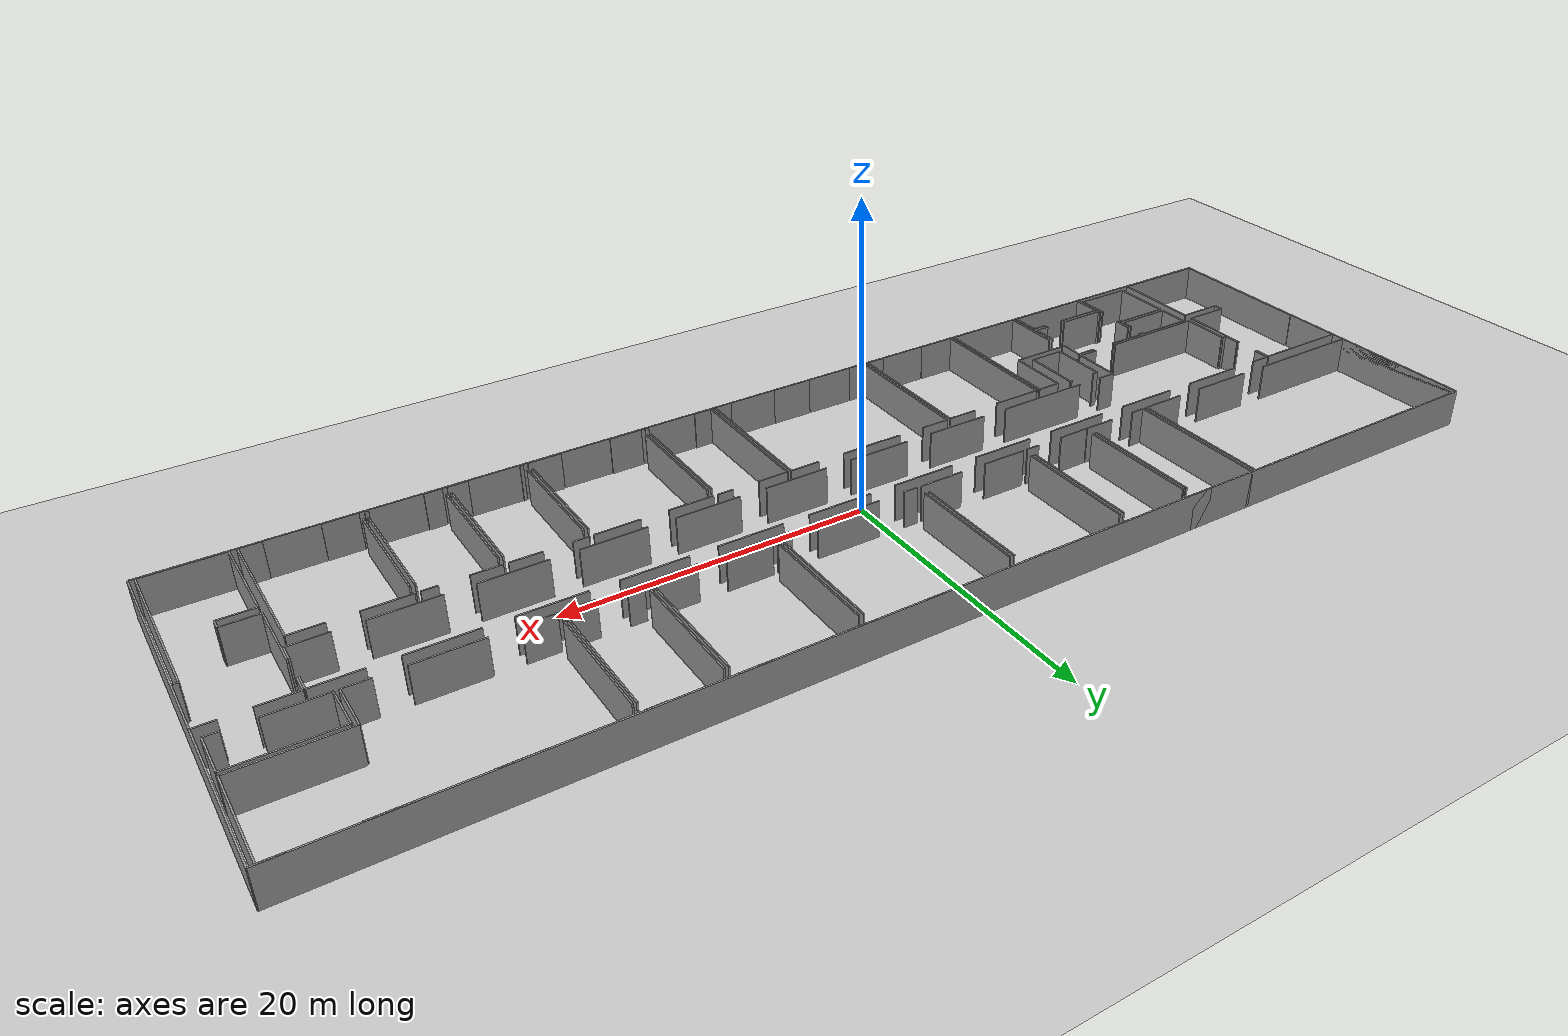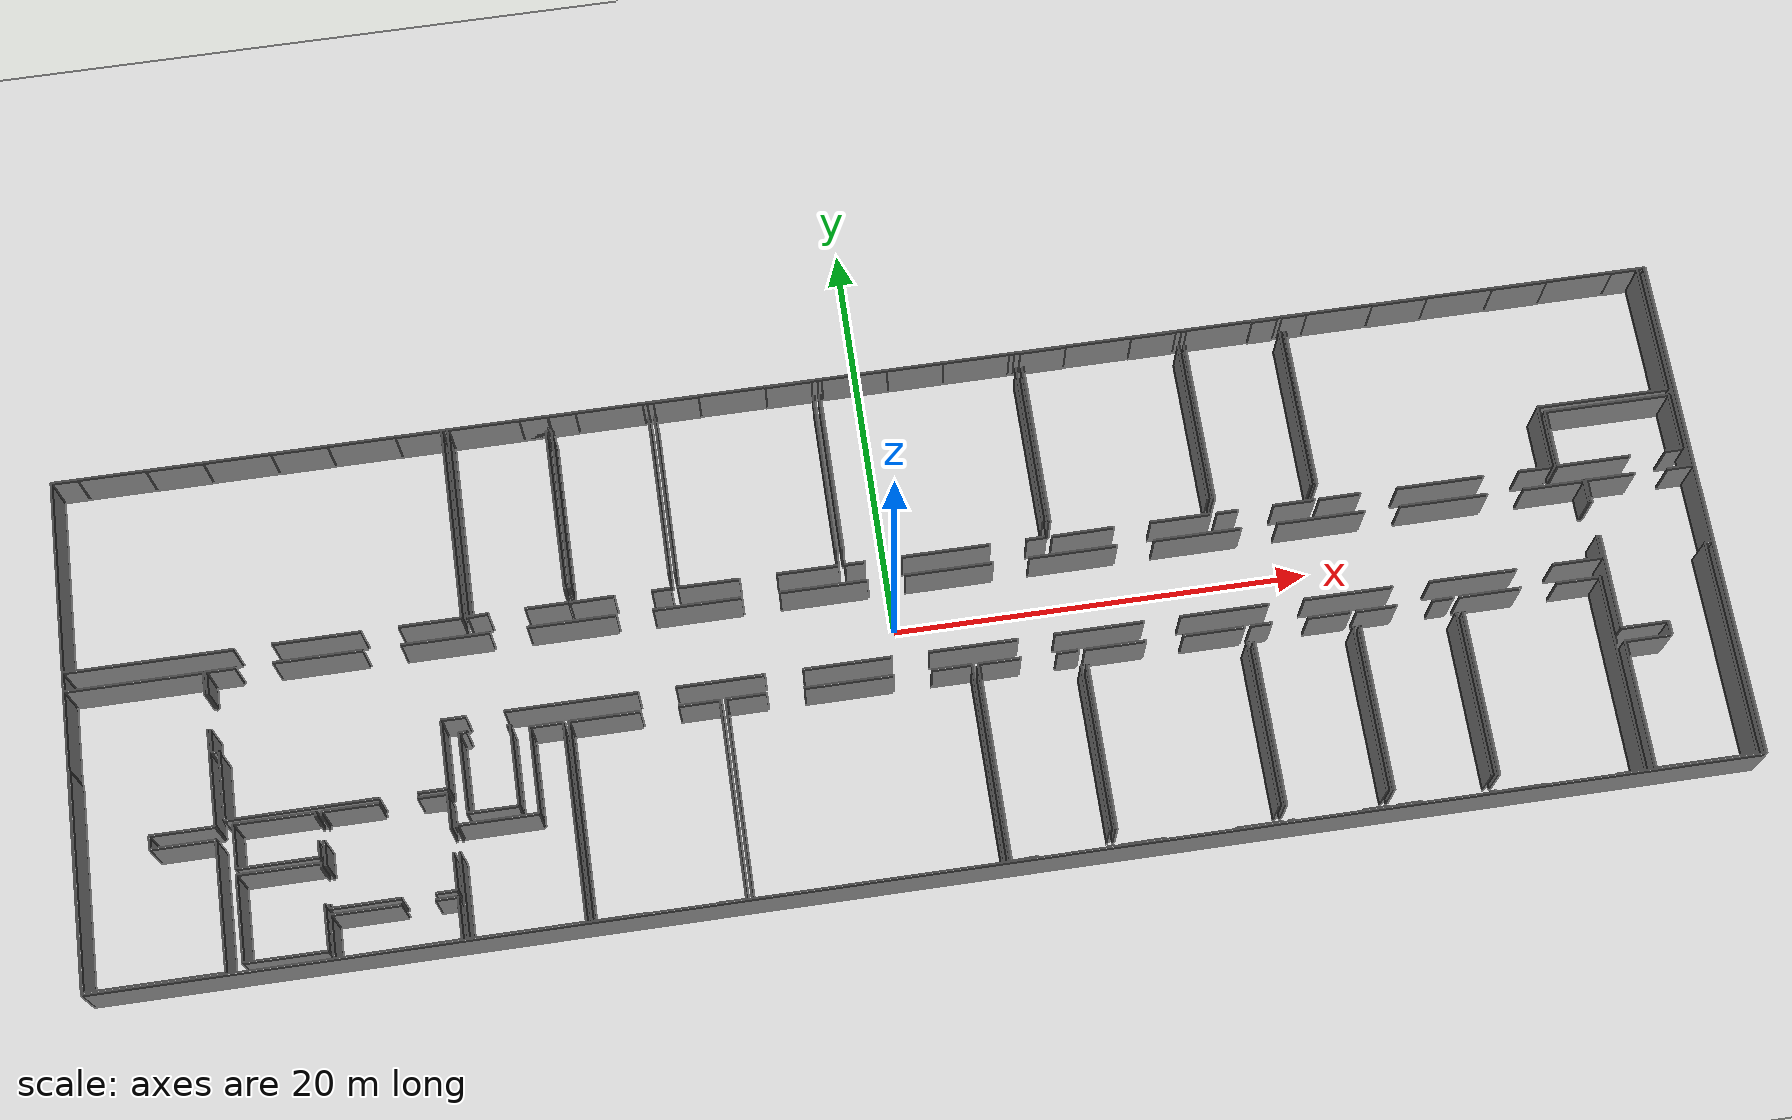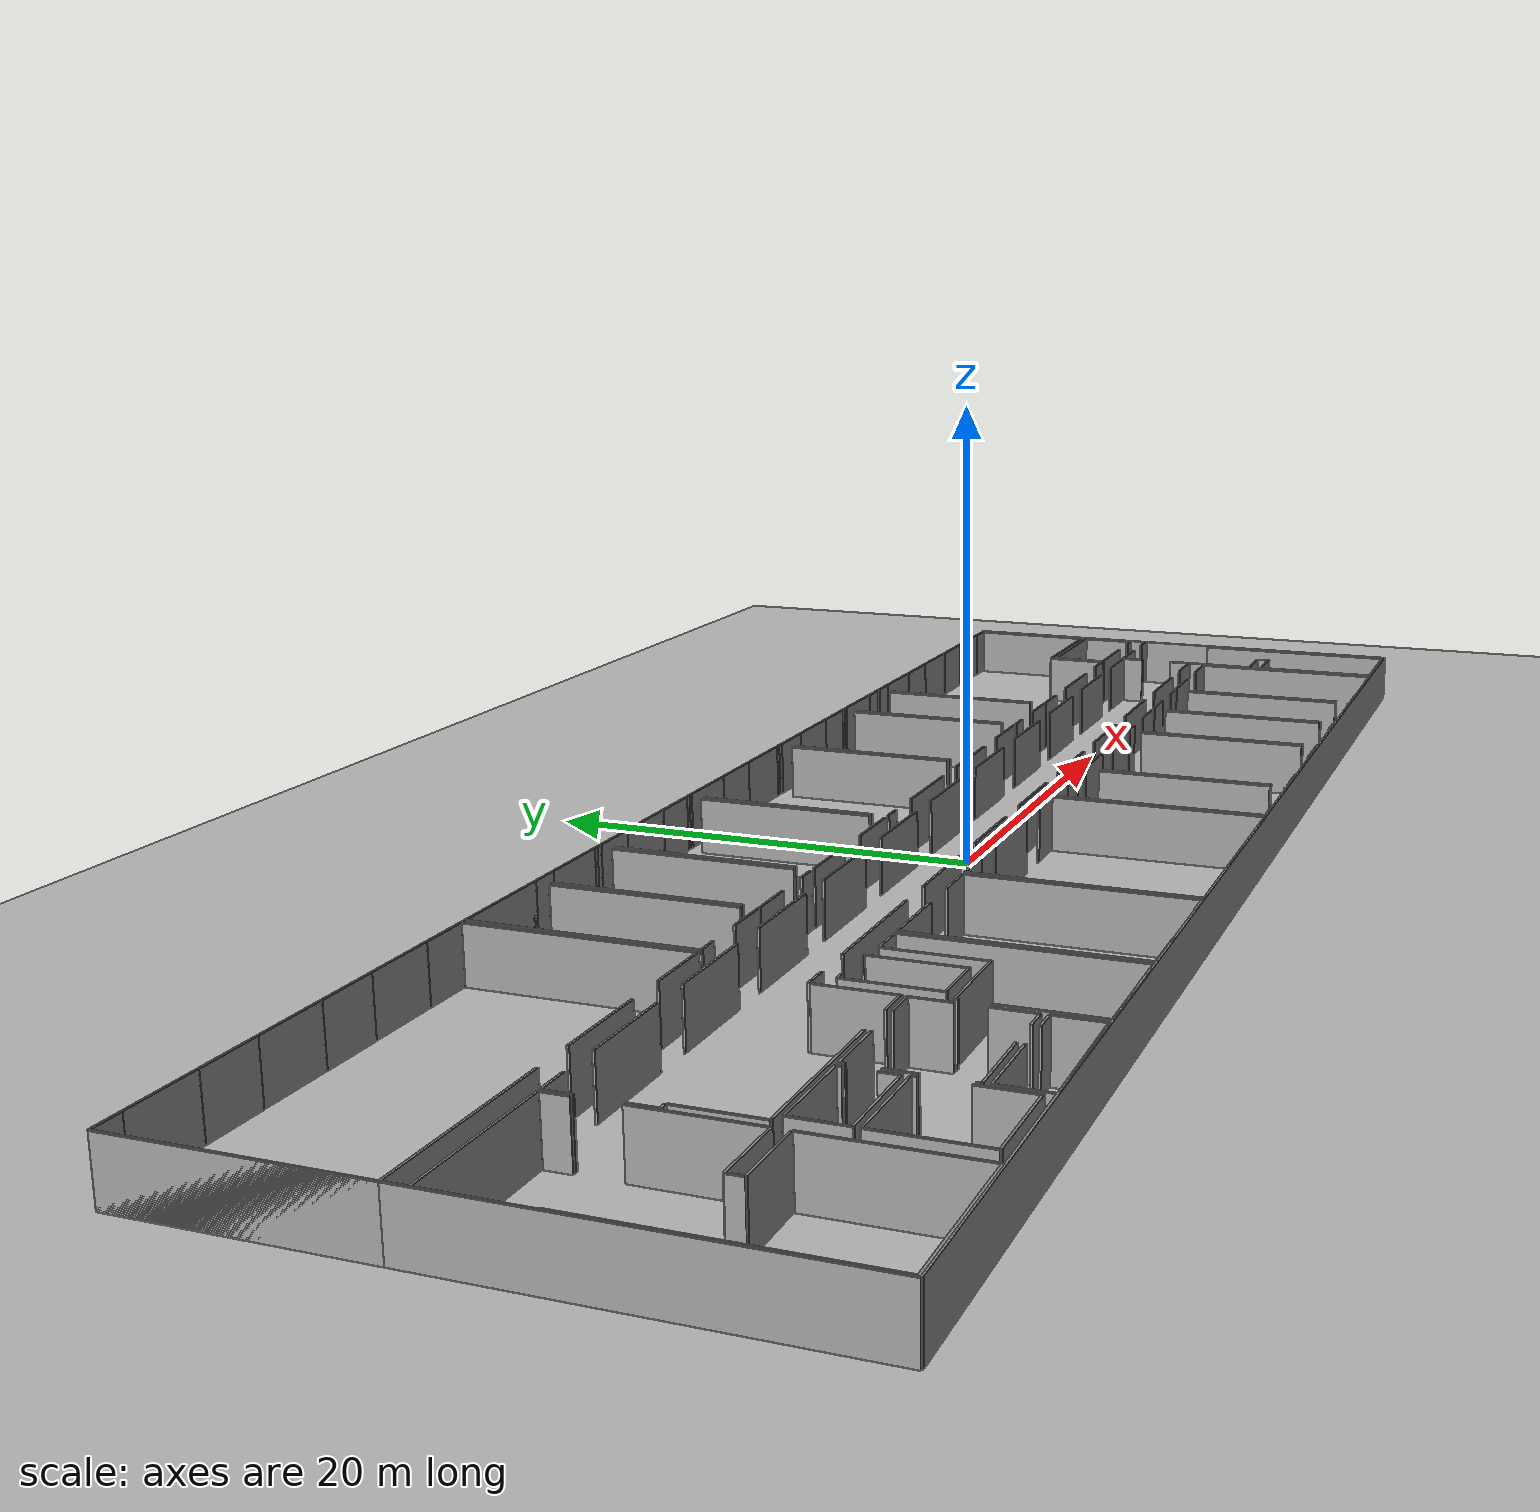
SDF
<sdf version="1.6">
  <world name="default">
    <light name="sun" type="directional">
      <cast_shadows>1</cast_shadows>
      <pose frame="">0 0 10 0 -0 0</pose>
      <diffuse>0.8 0.8 0.8 1</diffuse>
      <specular>0.1 0.1 0.1 1</specular>
      <attenuation>
        <range>1000</range>
        <constant>0.9</constant>
        <linear>0.01</linear>
        <quadratic>0.001</quadratic>
      </attenuation>
      <direction>-0.5 0.5 -1</direction>
    </light>
    <model name="ground_plane">
      <static>1</static>
      <link name="link">
        <collision name="collision">
          <geometry>
            <plane>
              <normal>0 0 1</normal>
              <size>100 100</size>
            </plane>
          </geometry>
          <surface>
            <friction>
              <ode>
                <mu>100</mu>
                <mu2>50</mu2>
              </ode>
              <torsional>
                <ode />
              </torsional>
            </friction>
            <contact>
              <ode />
            </contact>
            <bounce />
          </surface>
          <max_contacts>10</max_contacts>
        </collision>
        <visual name="visual">
          <cast_shadows>0</cast_shadows>
          <geometry>
            <plane>
              <normal>0 0 1</normal>
              <size>100 100</size>
            </plane>
          </geometry>
          <material>
            <script>
              <uri>file://media/materials/scripts/gazebo.material</uri>
              <name>Gazebo/Grey</name>
            </script>
          </material>
        </visual>
        <self_collide>0</self_collide>
        <kinematic>0</kinematic>
        <gravity>1</gravity>
      </link>
    </model>
    <gravity>0 0 -9.8</gravity>
    <magnetic_field>6e-06 2.3e-05 -4.2e-05</magnetic_field>
    <atmosphere type="adiabatic" />
    <physics default="0" name="default_physics" type="ode">
      <max_step_size>0.001</max_step_size>
      <real_time_factor>1</real_time_factor>
      <real_time_update_rate>1000</real_time_update_rate>
    </physics>
    <scene>
      <ambient>0.4 0.4 0.4 1</ambient>
      <background>0.7 0.7 0.7 1</background>
      <shadows>1</shadows>
    </scene>
    <spherical_coordinates>
      <surface_model>EARTH_WGS84</surface_model>
      <latitude_deg>0</latitude_deg>
      <longitude_deg>0</longitude_deg>
      <elevation>0</elevation>
      <heading_deg>0</heading_deg>
    </spherical_coordinates>
  <model name="50052752">
		<static>1</static>
		<link name="Wall_0">
			<collision name="Wall_0_Collision">
				<geometry>
					<box>
						<size>2.99465783496 0.1 2.5</size>
					</box>
				</geometry>
				<pose frame="">1.49732891748 0 1.25 0 0 0</pose>
			</collision>
			<visual name="Wall_0_Visual">
				<pose frame="">1.49732891748 0 1.25 0 0 0</pose>
				<geometry>
					<box>
						<size>2.99465783496 0.1 2.5</size>
					</box>
				</geometry>
				<material>
					<script>
						<uri>file://media/materials/scripts/gazebo.material</uri>
						<name>Gazebo/Grey</name>
					</script>
					<ambient>1 1 1 1</ambient>
				</material>
			</visual>
			<pose frame="">18.7927468372 -9.64381336683 0 0 0 3.14159265359</pose>
		</link>
		<link name="Wall_1">
			<collision name="Wall_1_Collision">
				<geometry>
					<box>
						<size>4.19290164579 0.1 2.5</size>
					</box>
				</geometry>
				<pose frame="">2.0964508229 0 1.25 0 0 0</pose>
			</collision>
			<visual name="Wall_1_Visual">
				<pose frame="">2.0964508229 0 1.25 0 0 0</pose>
				<geometry>
					<box>
						<size>4.19290164579 0.1 2.5</size>
					</box>
				</geometry>
				<material>
					<script>
						<uri>file://media/materials/scripts/gazebo.material</uri>
						<name>Gazebo/Grey</name>
					</script>
					<ambient>1 1 1 1</ambient>
				</material>
			</visual>
			<pose frame="">14.0342862944 -9.64381336683 0 0 0 3.14159265359</pose>
		</link>
		<link name="Wall_2">
			<collision name="Wall_2_Collision">
				<geometry>
					<box>
						<size>8.03228139632 0.1 2.5</size>
					</box>
				</geometry>
				<pose frame="">4.01614069816 0 1.25 0 0 0</pose>
			</collision>
			<visual name="Wall_2_Visual">
				<pose frame="">4.01614069816 0 1.25 0 0 0</pose>
				<geometry>
					<box>
						<size>8.03228139632 0.1 2.5</size>
					</box>
				</geometry>
				<material>
					<script>
						<uri>file://media/materials/scripts/gazebo.material</uri>
						<name>Gazebo/Grey</name>
					</script>
					<ambient>1 1 1 1</ambient>
				</material>
			</visual>
			<pose frame="">8.03228139632 -9.64381336683 0 0 0 3.14159265359</pose>
		</link>
		<link name="Wall_3">
			<collision name="Wall_3_Collision">
				<geometry>
					<box>
						<size>9.63277373837 0.1 2.5</size>
					</box>
				</geometry>
				<pose frame="">4.81638686919 0 1.25 0 0 0</pose>
			</collision>
			<visual name="Wall_3_Visual">
				<pose frame="">4.81638686919 0 1.25 0 0 0</pose>
				<geometry>
					<box>
						<size>9.63277373837 0.1 2.5</size>
					</box>
				</geometry>
				<material>
					<script>
						<uri>file://media/materials/scripts/gazebo.material</uri>
						<name>Gazebo/Grey</name>
					</script>
					<ambient>1 1 1 1</ambient>
				</material>
			</visual>
			<pose frame="">0.0 -9.64381336683 0 0 0 1.57079632679</pose>
		</link>
		<link name="Wall_4">
			<collision name="Wall_4_Collision">
				<geometry>
					<box>
						<size>1.27323714898 0.1 2.5</size>
					</box>
				</geometry>
				<pose frame="">0.636618574492 0 1.25 0 0 0</pose>
			</collision>
			<visual name="Wall_4_Visual">
				<pose frame="">0.636618574492 0 1.25 0 0 0</pose>
				<geometry>
					<box>
						<size>1.27323714898 0.1 2.5</size>
					</box>
				</geometry>
				<material>
					<script>
						<uri>file://media/materials/scripts/gazebo.material</uri>
						<name>Gazebo/Grey</name>
					</script>
					<ambient>1 1 1 1</ambient>
				</material>
			</visual>
			<pose frame="">0.0 -0.0110396284594 0 0 0 0.0</pose>
		</link>
		<link name="Wall_5">
			<collision name="Wall_5_Collision">
				<geometry>
					<box>
						<size>2.74975573236 0.1 2.5</size>
					</box>
				</geometry>
				<pose frame="">1.37487786618 0 1.25 0 0 0</pose>
			</collision>
			<visual name="Wall_5_Visual">
				<pose frame="">1.37487786618 0 1.25 0 0 0</pose>
				<geometry>
					<box>
						<size>2.74975573236 0.1 2.5</size>
					</box>
				</geometry>
				<material>
					<script>
						<uri>file://media/materials/scripts/gazebo.material</uri>
						<name>Gazebo/Grey</name>
					</script>
					<ambient>1 1 1 1</ambient>
				</material>
			</visual>
			<pose frame="">4.53513012803 -0.0110396284594 0 0 0 0.0</pose>
		</link>
		<link name="Wall_6">
			<collision name="Wall_6_Collision">
				<geometry>
					<box>
						<size>2.73516312003 0.1 2.5</size>
					</box>
				</geometry>
				<pose frame="">1.36758156001 0 1.25 0 0 0</pose>
			</collision>
			<visual name="Wall_6_Visual">
				<pose frame="">1.36758156001 0 1.25 0 0 0</pose>
				<geometry>
					<box>
						<size>2.73516312003 0.1 2.5</size>
					</box>
				</geometry>
				<material>
					<script>
						<uri>file://media/materials/scripts/gazebo.material</uri>
						<name>Gazebo/Grey</name>
					</script>
					<ambient>1 1 1 1</ambient>
				</material>
			</visual>
			<pose frame="">10.5278718896 -0.0110396284594 0 0 0 0.0</pose>
		</link>
		<link name="Wall_7">
			<collision name="Wall_7_Collision">
				<geometry>
					<box>
						<size>2.25639854328 0.1 2.5</size>
					</box>
				</geometry>
				<pose frame="">1.12819927164 0 1.25 0 0 0</pose>
			</collision>
			<visual name="Wall_7_Visual">
				<pose frame="">1.12819927164 0 1.25 0 0 0</pose>
				<geometry>
					<box>
						<size>2.25639854328 0.1 2.5</size>
					</box>
				</geometry>
				<material>
					<script>
						<uri>file://media/materials/scripts/gazebo.material</uri>
						<name>Gazebo/Grey</name>
					</script>
					<ambient>1 1 1 1</ambient>
				</material>
			</visual>
			<pose frame="">16.5350793711 -0.0110396284594 0 0 0 0.0</pose>
		</link>
		<link name="Wall_8">
			<collision name="Wall_8_Collision">
				<geometry>
					<box>
						<size>9.63277382195 0.1 2.5</size>
					</box>
				</geometry>
				<pose frame="">4.81638691098 0 1.25 0 0 0</pose>
			</collision>
			<visual name="Wall_8_Visual">
				<pose frame="">4.81638691098 0 1.25 0 0 0</pose>
				<geometry>
					<box>
						<size>9.63277382195 0.1 2.5</size>
					</box>
				</geometry>
				<material>
					<script>
						<uri>file://media/materials/scripts/gazebo.material</uri>
						<name>Gazebo/Grey</name>
					</script>
					<ambient>1 1 1 1</ambient>
				</material>
			</visual>
			<pose frame="">18.7914779144 -0.0110396284594 0 0 0 -1.57066459705</pose>
		</link>
		<link name="Wall_9">
			<collision name="Wall_9_Collision">
				<geometry>
					<box>
						<size>10.5219079523 0.1 2.5</size>
					</box>
				</geometry>
				<pose frame="">5.26095397617 0 1.25 0 0 0</pose>
			</collision>
			<visual name="Wall_9_Visual">
				<pose frame="">5.26095397617 0 1.25 0 0 0</pose>
				<geometry>
					<box>
						<size>10.5219079523 0.1 2.5</size>
					</box>
				</geometry>
				<material>
					<script>
						<uri>file://media/materials/scripts/gazebo.material</uri>
						<name>Gazebo/Grey</name>
					</script>
					<ambient>1 1 1 1</ambient>
				</material>
			</visual>
			<pose frame="">0.0477114977096 -25.0307713782 0 0 0 1.57079632679</pose>
		</link>
		<link name="Wall_10">
			<collision name="Wall_10_Collision">
				<geometry>
					<box>
						<size>6.49993020925 0.1 2.5</size>
					</box>
				</geometry>
				<pose frame="">3.24996510462 0 1.25 0 0 0</pose>
			</collision>
			<visual name="Wall_10_Visual">
				<pose frame="">3.24996510462 0 1.25 0 0 0</pose>
				<geometry>
					<box>
						<size>6.49993020925 0.1 2.5</size>
					</box>
				</geometry>
				<material>
					<script>
						<uri>file://media/materials/scripts/gazebo.material</uri>
						<name>Gazebo/Grey</name>
					</script>
					<ambient>1 1 1 1</ambient>
				</material>
			</visual>
			<pose frame="">0.0477114977096 -10.5749489259 0 0 0 0.0</pose>
		</link>
		<link name="Wall_11">
			<collision name="Wall_11_Collision">
				<geometry>
					<box>
						<size>1.074650729 0.1 2.5</size>
					</box>
				</geometry>
				<pose frame="">0.537325364498 0 1.25 0 0 0</pose>
			</collision>
			<visual name="Wall_11_Visual">
				<pose frame="">0.537325364498 0 1.25 0 0 0</pose>
				<geometry>
					<box>
						<size>1.074650729 0.1 2.5</size>
					</box>
				</geometry>
				<material>
					<script>
						<uri>file://media/materials/scripts/gazebo.material</uri>
						<name>Gazebo/Grey</name>
					</script>
					<ambient>1 1 1 1</ambient>
				</material>
			</visual>
			<pose frame="">6.54764170695 -10.5749489259 0 0 0 -1.57079632679</pose>
		</link>
		<link name="Wall_12">
			<collision name="Wall_12_Collision">
				<geometry>
					<box>
						<size>4.73371654802 0.1 2.5</size>
					</box>
				</geometry>
				<pose frame="">2.36685827401 0 1.25 0 0 0</pose>
			</collision>
			<visual name="Wall_12_Visual">
				<pose frame="">2.36685827401 0 1.25 0 0 0</pose>
				<geometry>
					<box>
						<size>4.73371654802 0.1 2.5</size>
					</box>
				</geometry>
				<material>
					<script>
						<uri>file://media/materials/scripts/gazebo.material</uri>
						<name>Gazebo/Grey</name>
					</script>
					<ambient>1 1 1 1</ambient>
				</material>
			</visual>
			<pose frame="">6.54764170695 -13.3843440304 0 0 0 -1.57079632679</pose>
		</link>
		<link name="Wall_13">
			<collision name="Wall_13_Collision">
				<geometry>
					<box>
						<size>3.04655677795 0.1 2.5</size>
					</box>
				</geometry>
				<pose frame="">1.52327838898 0 1.25 0 0 0</pose>
			</collision>
			<visual name="Wall_13_Visual">
				<pose frame="">1.52327838898 0 1.25 0 0 0</pose>
				<geometry>
					<box>
						<size>3.04655677795 0.1 2.5</size>
					</box>
				</geometry>
				<material>
					<script>
						<uri>file://media/materials/scripts/gazebo.material</uri>
						<name>Gazebo/Grey</name>
					</script>
					<ambient>1 1 1 1</ambient>
				</material>
			</visual>
			<pose frame="">6.54764170695 -18.1180605784 0 0 0 3.14159265359</pose>
		</link>
		<link name="Wall_14">
			<collision name="Wall_14_Collision">
				<geometry>
					<box>
						<size>0.639917773802 0.1 2.5</size>
					</box>
				</geometry>
				<pose frame="">0.319958886901 0 1.25 0 0 0</pose>
			</collision>
			<visual name="Wall_14_Visual">
				<pose frame="">0.319958886901 0 1.25 0 0 0</pose>
				<geometry>
					<box>
						<size>0.639917773802 0.1 2.5</size>
					</box>
				</geometry>
				<material>
					<script>
						<uri>file://media/materials/scripts/gazebo.material</uri>
						<name>Gazebo/Grey</name>
					</script>
					<ambient>1 1 1 1</ambient>
				</material>
			</visual>
			<pose frame="">3.501084929 -18.1180605784 0 0 0 -1.57079632679</pose>
		</link>
		<link name="Wall_15">
			<collision name="Wall_15_Collision">
				<geometry>
					<box>
						<size>3.03437511896 0.1 2.5</size>
					</box>
				</geometry>
				<pose frame="">1.51718755948 0 1.25 0 0 0</pose>
			</collision>
			<visual name="Wall_15_Visual">
				<pose frame="">1.51718755948 0 1.25 0 0 0</pose>
				<geometry>
					<box>
						<size>3.03437511896 0.1 2.5</size>
					</box>
				</geometry>
				<material>
					<script>
						<uri>file://media/materials/scripts/gazebo.material</uri>
						<name>Gazebo/Grey</name>
					</script>
					<ambient>1 1 1 1</ambient>
				</material>
			</visual>
			<pose frame="">3.501084929 -18.7579783522 0 0 0 0.0</pose>
		</link>
		<link name="Wall_16">
			<collision name="Wall_16_Collision">
				<geometry>
					<box>
						<size>6.27837628637 0.1 2.5</size>
					</box>
				</geometry>
				<pose frame="">3.13918814319 0 1.25 0 0 0</pose>
			</collision>
			<visual name="Wall_16_Visual">
				<pose frame="">3.13918814319 0 1.25 0 0 0</pose>
				<geometry>
					<box>
						<size>6.27837628637 0.1 2.5</size>
					</box>
				</geometry>
				<material>
					<script>
						<uri>file://media/materials/scripts/gazebo.material</uri>
						<name>Gazebo/Grey</name>
					</script>
					<ambient>1 1 1 1</ambient>
				</material>
			</visual>
			<pose frame="">6.53546004797 -18.7579783522 0 0 0 -1.57079632679</pose>
		</link>
		<link name="Wall_17">
			<collision name="Wall_17_Collision">
				<geometry>
					<box>
						<size>6.48775095269 0.1 2.5</size>
					</box>
				</geometry>
				<pose frame="">3.24387547635 0 1.25 0 0 0</pose>
			</collision>
			<visual name="Wall_17_Visual">
				<pose frame="">3.24387547635 0 1.25 0 0 0</pose>
				<geometry>
					<box>
						<size>6.48775095269 0.1 2.5</size>
					</box>
				</geometry>
				<material>
					<script>
						<uri>file://media/materials/scripts/gazebo.material</uri>
						<name>Gazebo/Grey</name>
					</script>
					<ambient>1 1 1 1</ambient>
				</material>
			</visual>
			<pose frame="">6.53546004797 -25.0363546385 0 0 0 3.1407320686</pose>
		</link>
		<link name="Wall_18">
			<collision name="Wall_18_Collision">
				<geometry>
					<box>
						<size>1.14647176012 0.1 2.5</size>
					</box>
				</geometry>
				<pose frame="">0.573235880061 0 1.25 0 0 0</pose>
			</collision>
			<visual name="Wall_18_Visual">
				<pose frame="">0.573235880061 0 1.25 0 0 0</pose>
				<geometry>
					<box>
						<size>1.14647176012 0.1 2.5</size>
					</box>
				</geometry>
				<material>
					<script>
						<uri>file://media/materials/scripts/gazebo.material</uri>
						<name>Gazebo/Grey</name>
					</script>
					<ambient>1 1 1 1</ambient>
				</material>
			</visual>
			<pose frame="">6.65664217646 -14.5567018158 0 0 0 1.57079632679</pose>
		</link>
		<link name="Wall_19">
			<collision name="Wall_19_Collision">
				<geometry>
					<box>
						<size>1.11728653546 0.1 2.5</size>
					</box>
				</geometry>
				<pose frame="">0.55864326773 0 1.25 0 0 0</pose>
			</collision>
			<visual name="Wall_19_Visual">
				<pose frame="">0.55864326773 0 1.25 0 0 0</pose>
				<geometry>
					<box>
						<size>1.11728653546 0.1 2.5</size>
					</box>
				</geometry>
				<material>
					<script>
						<uri>file://media/materials/scripts/gazebo.material</uri>
						<name>Gazebo/Grey</name>
					</script>
					<ambient>1 1 1 1</ambient>
				</material>
			</visual>
			<pose frame="">6.65664217646 -11.6824647557 0 0 0 1.57079632679</pose>
		</link>
		<link name="Wall_20">
			<collision name="Wall_20_Collision">
				<geometry>
					<box>
						<size>1.38274518761 0.1 2.5</size>
					</box>
				</geometry>
				<pose frame="">0.691372593805 0 1.25 0 0 0</pose>
			</collision>
			<visual name="Wall_20_Visual">
				<pose frame="">0.691372593805 0 1.25 0 0 0</pose>
				<geometry>
					<box>
						<size>1.38274518761 0.1 2.5</size>
					</box>
				</geometry>
				<material>
					<script>
						<uri>file://media/materials/scripts/gazebo.material</uri>
						<name>Gazebo/Grey</name>
					</script>
					<ambient>1 1 1 1</ambient>
				</material>
			</visual>
			<pose frame="">6.65664217646 -10.5651782202 0 0 0 0.0</pose>
		</link>
		<link name="Wall_21">
			<collision name="Wall_21_Collision">
				<geometry>
					<box>
						<size>4.23135000698 0.1 2.5</size>
					</box>
				</geometry>
				<pose frame="">2.11567500349 0 1.25 0 0 0</pose>
			</collision>
			<visual name="Wall_21_Visual">
				<pose frame="">2.11567500349 0 1.25 0 0 0</pose>
				<geometry>
					<box>
						<size>4.23135000698 0.1 2.5</size>
					</box>
				</geometry>
				<material>
					<script>
						<uri>file://media/materials/scripts/gazebo.material</uri>
						<name>Gazebo/Grey</name>
					</script>
					<ambient>1 1 1 1</ambient>
				</material>
			</visual>
			<pose frame="">9.80306317967 -10.5651782202 0 0 0 0.0</pose>
		</link>
		<link name="Wall_22">
			<collision name="Wall_22_Collision">
				<geometry>
					<box>
						<size>4.20076896722 0.1 2.5</size>
					</box>
				</geometry>
				<pose frame="">2.10038448361 0 1.25 0 0 0</pose>
			</collision>
			<visual name="Wall_22_Visual">
				<pose frame="">2.10038448361 0 1.25 0 0 0</pose>
				<geometry>
					<box>
						<size>4.20076896722 0.1 2.5</size>
					</box>
				</geometry>
				<material>
					<script>
						<uri>file://media/materials/scripts/gazebo.material</uri>
						<name>Gazebo/Grey</name>
					</script>
					<ambient>1 1 1 1</ambient>
				</material>
			</visual>
			<pose frame="">15.8241019199 -10.5651782202 0 0 0 0.0</pose>
		</link>
		<link name="Wall_23">
			<collision name="Wall_23_Collision">
				<geometry>
					<box>
						<size>4.22614742345 0.1 2.5</size>
					</box>
				</geometry>
				<pose frame="">2.11307371173 0 1.25 0 0 0</pose>
			</collision>
			<visual name="Wall_23_Visual">
				<pose frame="">2.11307371173 0 1.25 0 0 0</pose>
				<geometry>
					<box>
						<size>4.22614742345 0.1 2.5</size>
					</box>
				</geometry>
				<material>
					<script>
						<uri>file://media/materials/scripts/gazebo.material</uri>
						<name>Gazebo/Grey</name>
					</script>
					<ambient>1 1 1 1</ambient>
				</material>
			</visual>
			<pose frame="">21.8066922989 -10.5651782202 0 0 0 0.0</pose>
		</link>
		<link name="Wall_24">
			<collision name="Wall_24_Collision">
				<geometry>
					<box>
						<size>4.23706015963 0.1 2.5</size>
					</box>
				</geometry>
				<pose frame="">2.11853007982 0 1.25 0 0 0</pose>
			</collision>
			<visual name="Wall_24_Visual">
				<pose frame="">2.11853007982 0 1.25 0 0 0</pose>
				<geometry>
					<box>
						<size>4.23706015963 0.1 2.5</size>
					</box>
				</geometry>
				<material>
					<script>
						<uri>file://media/materials/scripts/gazebo.material</uri>
						<name>Gazebo/Grey</name>
					</script>
					<ambient>1 1 1 1</ambient>
				</material>
			</visual>
			<pose frame="">27.7805271105 -10.5651782202 0 0 0 0.0</pose>
		</link>
		<link name="Wall_25">
			<collision name="Wall_25_Collision">
				<geometry>
					<box>
						<size>4.22893905364 0.1 2.5</size>
					</box>
				</geometry>
				<pose frame="">2.11446952682 0 1.25 0 0 0</pose>
			</collision>
			<visual name="Wall_25_Visual">
				<pose frame="">2.11446952682 0 1.25 0 0 0</pose>
				<geometry>
					<box>
						<size>4.22893905364 0.1 2.5</size>
					</box>
				</geometry>
				<material>
					<script>
						<uri>file://media/materials/scripts/gazebo.material</uri>
						<name>Gazebo/Grey</name>
					</script>
					<ambient>1 1 1 1</ambient>
				</material>
			</visual>
			<pose frame="">33.8048650501 -10.5651782202 0 0 0 0.0</pose>
		</link>
		<link name="Wall_26">
			<collision name="Wall_26_Collision">
				<geometry>
					<box>
						<size>4.23820219016 0.1 2.5</size>
					</box>
				</geometry>
				<pose frame="">2.11910109508 0 1.25 0 0 0</pose>
			</collision>
			<visual name="Wall_26_Visual">
				<pose frame="">2.11910109508 0 1.25 0 0 0</pose>
				<geometry>
					<box>
						<size>4.23820219016 0.1 2.5</size>
					</box>
				</geometry>
				<material>
					<script>
						<uri>file://media/materials/scripts/gazebo.material</uri>
						<name>Gazebo/Grey</name>
					</script>
					<ambient>1 1 1 1</ambient>
				</material>
			</visual>
			<pose frame="">39.7934193663 -10.5651782202 0 0 0 0.0</pose>
		</link>
		<link name="Wall_27">
			<collision name="Wall_27_Collision">
				<geometry>
					<box>
						<size>4.2318575761 0.1 2.5</size>
					</box>
				</geometry>
				<pose frame="">2.11592878805 0 1.25 0 0 0</pose>
			</collision>
			<visual name="Wall_27_Visual">
				<pose frame="">2.11592878805 0 1.25 0 0 0</pose>
				<geometry>
					<box>
						<size>4.2318575761 0.1 2.5</size>
					</box>
				</geometry>
				<material>
					<script>
						<uri>file://media/materials/scripts/gazebo.material</uri>
						<name>Gazebo/Grey</name>
					</script>
					<ambient>1 1 1 1</ambient>
				</material>
			</visual>
			<pose frame="">45.7694113467 -10.5651782202 0 0 0 0.0</pose>
		</link>
		<link name="Wall_28">
			<collision name="Wall_28_Collision">
				<geometry>
					<box>
						<size>4.22678188486 0.1 2.5</size>
					</box>
				</geometry>
				<pose frame="">2.11339094243 0 1.25 0 0 0</pose>
			</collision>
			<visual name="Wall_28_Visual">
				<pose frame="">2.11339094243 0 1.25 0 0 0</pose>
				<geometry>
					<box>
						<size>4.22678188486 0.1 2.5</size>
					</box>
				</geometry>
				<material>
					<script>
						<uri>file://media/materials/scripts/gazebo.material</uri>
						<name>Gazebo/Grey</name>
					</script>
					<ambient>1 1 1 1</ambient>
				</material>
			</visual>
			<pose frame="">51.7961602396 -10.5651782202 0 0 0 0.0</pose>
		</link>
		<link name="Wall_29">
			<collision name="Wall_29_Collision">
				<geometry>
					<box>
						<size>4.22208687046 0.1 2.5</size>
					</box>
				</geometry>
				<pose frame="">2.11104343523 0 1.25 0 0 0</pose>
			</collision>
			<visual name="Wall_29_Visual">
				<pose frame="">2.11104343523 0 1.25 0 0 0</pose>
				<geometry>
					<box>
						<size>4.22208687046 0.1 2.5</size>
					</box>
				</geometry>
				<material>
					<script>
						<uri>file://media/materials/scripts/gazebo.material</uri>
						<name>Gazebo/Grey</name>
					</script>
					<ambient>1 1 1 1</ambient>
				</material>
			</visual>
			<pose frame="">57.7867448323 -10.5651782202 0 0 0 0.0</pose>
		</link>
		<link name="Wall_30">
			<collision name="Wall_30_Collision">
				<geometry>
					<box>
						<size>4.24809978809 0.1 2.5</size>
					</box>
				</geometry>
				<pose frame="">2.12404989404 0 1.25 0 0 0</pose>
			</collision>
			<visual name="Wall_30_Visual">
				<pose frame="">2.12404989404 0 1.25 0 0 0</pose>
				<geometry>
					<box>
						<size>4.24809978809 0.1 2.5</size>
					</box>
				</geometry>
				<material>
					<script>
						<uri>file://media/materials/scripts/gazebo.material</uri>
						<name>Gazebo/Grey</name>
					</script>
					<ambient>1 1 1 1</ambient>
				</material>
			</visual>
			<pose frame="">63.7473828467 -10.5651782202 0 0 0 0.0</pose>
		</link>
		<link name="Wall_31">
			<collision name="Wall_31_Collision">
				<geometry>
					<box>
						<size>2.96927937874 0.1 2.5</size>
					</box>
				</geometry>
				<pose frame="">1.48463968937 0 1.25 0 0 0</pose>
			</collision>
			<visual name="Wall_31_Visual">
				<pose frame="">1.48463968937 0 1.25 0 0 0</pose>
				<geometry>
					<box>
						<size>2.96927937874 0.1 2.5</size>
					</box>
				</geometry>
				<material>
					<script>
						<uri>file://media/materials/scripts/gazebo.material</uri>
						<name>Gazebo/Grey</name>
					</script>
					<ambient>1 1 1 1</ambient>
				</material>
			</visual>
			<pose frame="">69.7780654003 -10.5651782202 0 0 0 0.0</pose>
		</link>
		<link name="Wall_32">
			<collision name="Wall_32_Collision">
				<geometry>
					<box>
						<size>1.13238671692 0.1 2.5</size>
					</box>
				</geometry>
				<pose frame="">0.566193358458 0 1.25 0 0 0</pose>
			</collision>
			<visual name="Wall_32_Visual">
				<pose frame="">0.566193358458 0 1.25 0 0 0</pose>
				<geometry>
					<box>
						<size>1.13238671692 0.1 2.5</size>
					</box>
				</geometry>
				<material>
					<script>
						<uri>file://media/materials/scripts/gazebo.material</uri>
						<name>Gazebo/Grey</name>
					</script>
					<ambient>1 1 1 1</ambient>
				</material>
			</visual>
			<pose frame="">72.747344779 -10.5651782202 0 0 0 -1.57079632679</pose>
		</link>
		<link name="Wall_33">
			<collision name="Wall_33_Collision">
				<geometry>
					<box>
						<size>1.12553453373 0.1 2.5</size>
					</box>
				</geometry>
				<pose frame="">0.562767266867 0 1.25 0 0 0</pose>
			</collision>
			<visual name="Wall_33_Visual">
				<pose frame="">0.562767266867 0 1.25 0 0 0</pose>
				<geometry>
					<box>
						<size>1.12553453373 0.1 2.5</size>
					</box>
				</geometry>
				<material>
					<script>
						<uri>file://media/materials/scripts/gazebo.material</uri>
						<name>Gazebo/Grey</name>
					</script>
					<ambient>1 1 1 1</ambient>
				</material>
			</visual>
			<pose frame="">72.747344779 -13.3953836588 0 0 0 -1.57079632679</pose>
		</link>
		<link name="Wall_34">
			<collision name="Wall_34_Collision">
				<geometry>
					<box>
						<size>2.4015633129 0.1 2.5</size>
					</box>
				</geometry>
				<pose frame="">1.20078165645 0 1.25 0 0 0</pose>
			</collision>
			<visual name="Wall_34_Visual">
				<pose frame="">1.20078165645 0 1.25 0 0 0</pose>
				<geometry>
					<box>
						<size>2.4015633129 0.1 2.5</size>
					</box>
				</geometry>
				<material>
					<script>
						<uri>file://media/materials/scripts/gazebo.material</uri>
						<name>Gazebo/Grey</name>
					</script>
					<ambient>1 1 1 1</ambient>
				</material>
			</visual>
			<pose frame="">72.747344779 -14.5209181925 0 0 0 3.14159265359</pose>
		</link>
		<link name="Wall_35">
			<collision name="Wall_35_Collision">
				<geometry>
					<box>
						<size>4.18807973911 0.1 2.5</size>
					</box>
				</geometry>
				<pose frame="">2.09403986955 0 1.25 0 0 0</pose>
			</collision>
			<visual name="Wall_35_Visual">
				<pose frame="">2.09403986955 0 1.25 0 0 0</pose>
				<geometry>
					<box>
						<size>4.18807973911 0.1 2.5</size>
					</box>
				</geometry>
				<material>
					<script>
						<uri>file://media/materials/scripts/gazebo.material</uri>
						<name>Gazebo/Grey</name>
					</script>
					<ambient>1 1 1 1</ambient>
				</material>
			</visual>
			<pose frame="">68.5630718083 -14.5209181925 0 0 0 3.14159265359</pose>
		</link>
		<link name="Wall_36">
			<collision name="Wall_36_Collision">
				<geometry>
					<box>
						<size>4.23135000698 0.1 2.5</size>
					</box>
				</geometry>
				<pose frame="">2.11567500349 0 1.25 0 0 0</pose>
			</collision>
			<visual name="Wall_36_Visual">
				<pose frame="">2.11567500349 0 1.25 0 0 0</pose>
				<geometry>
					<box>
						<size>4.23135000698 0.1 2.5</size>
					</box>
				</geometry>
				<material>
					<script>
						<uri>file://media/materials/scripts/gazebo.material</uri>
						<name>Gazebo/Grey</name>
					</script>
					<ambient>1 1 1 1</ambient>
				</material>
			</visual>
			<pose frame="">62.5652543556 -14.5209181925 0 0 0 3.14159265359</pose>
		</link>
		<link name="Wall_37">
			<collision name="Wall_37_Collision">
				<geometry>
					<box>
						<size>4.22551296205 0.1 2.5</size>
					</box>
				</geometry>
				<pose frame="">2.11275648102 0 1.25 0 0 0</pose>
			</collision>
			<visual name="Wall_37_Visual">
				<pose frame="">2.11275648102 0 1.25 0 0 0</pose>
				<geometry>
					<box>
						<size>4.22551296205 0.1 2.5</size>
					</box>
				</geometry>
				<material>
					<script>
						<uri>file://media/materials/scripts/gazebo.material</uri>
						<name>Gazebo/Grey</name>
					</script>
					<ambient>1 1 1 1</ambient>
				</material>
			</visual>
			<pose frame="">56.5939573896 -14.5209181925 0 0 0 3.14159265359</pose>
		</link>
		<link name="Wall_38">
			<collision name="Wall_38_Collision">
				<geometry>
					<box>
						<size>4.25051074143 0.1 2.5</size>
					</box>
				</geometry>
				<pose frame="">2.12525537072 0 1.25 0 0 0</pose>
			</collision>
			<visual name="Wall_38_Visual">
				<pose frame="">2.12525537072 0 1.25 0 0 0</pose>
				<geometry>
					<box>
						<size>4.25051074143 0.1 2.5</size>
					</box>
				</geometry>
				<material>
					<script>
						<uri>file://media/materials/scripts/gazebo.material</uri>
						<name>Gazebo/Grey</name>
					</script>
					<ambient>1 1 1 1</ambient>
				</material>
			</visual>
			<pose frame="">50.6004542744 -14.5209181925 0 0 0 3.14159265359</pose>
		</link>
		<link name="Wall_39">
			<collision name="Wall_39_Collision">
				<geometry>
					<box>
						<size>4.21218927253 0.1 2.5</size>
					</box>
				</geometry>
				<pose frame="">2.10609463626 0 1.25 0 0 0</pose>
			</collision>
			<visual name="Wall_39_Visual">
				<pose frame="">2.10609463626 0 1.25 0 0 0</pose>
				<geometry>
					<box>
						<size>4.21218927253 0.1 2.5</size>
					</box>
				</geometry>
				<material>
					<script>
						<uri>file://media/materials/scripts/gazebo.material</uri>
						<name>Gazebo/Grey</name>
					</script>
					<ambient>1 1 1 1</ambient>
				</material>
			</visual>
			<pose frame="">44.5844912254 -14.5209181925 0 0 0 3.14159265359</pose>
		</link>
		<link name="Wall_40">
			<collision name="Wall_40_Collision">
				<geometry>
					<box>
						<size>4.19670841423 0.1 2.5</size>
					</box>
				</geometry>
				<pose frame="">2.09835420711 0 1.25 0 0 0</pose>
			</collision>
			<visual name="Wall_40_Visual">
				<pose frame="">2.09835420711 0 1.25 0 0 0</pose>
				<geometry>
					<box>
						<size>4.19670841423 0.1 2.5</size>
					</box>
				</geometry>
				<material>
					<script>
						<uri>file://media/materials/scripts/gazebo.material</uri>
						<name>Gazebo/Grey</name>
					</script>
					<ambient>1 1 1 1</ambient>
				</material>
			</visual>
			<pose frame="">38.5826132196 -14.5209181925 0 0 0 3.14159265359</pose>
		</link>
		<link name="Wall_41">
			<collision name="Wall_41_Collision">
				<geometry>
					<box>
						<size>4.20254545916 0.1 2.5</size>
					</box>
				</geometry>
				<pose frame="">2.10127272958 0 1.25 0 0 0</pose>
			</collision>
			<visual name="Wall_41_Visual">
				<pose frame="">2.10127272958 0 1.25 0 0 0</pose>
				<geometry>
					<box>
						<size>4.20254545916 0.1 2.5</size>
					</box>
				</geometry>
				<material>
					<script>
						<uri>file://media/materials/scripts/gazebo.material</uri>
						<name>Gazebo/Grey</name>
					</script>
					<ambient>1 1 1 1</ambient>
				</material>
			</visual>
			<pose frame="">32.581242783 -14.5209181925 0 0 0 3.14159265359</pose>
		</link>
		<link name="Wall_42">
			<collision name="Wall_42_Collision">
				<geometry>
					<box>
						<size>6.28941591483 0.1 2.5</size>
					</box>
				</geometry>
				<pose frame="">3.14470795741 0 1.25 0 0 0</pose>
			</collision>
			<visual name="Wall_42_Visual">
				<pose frame="">3.14470795741 0 1.25 0 0 0</pose>
				<geometry>
					<box>
						<size>6.28941591483 0.1 2.5</size>
					</box>
				</geometry>
				<material>
					<script>
						<uri>file://media/materials/scripts/gazebo.material</uri>
						<name>Gazebo/Grey</name>
					</script>
					<ambient>1 1 1 1</ambient>
				</material>
			</visual>
			<pose frame="">26.5947187433 -14.5209181925 0 0 0 3.14159265359</pose>
		</link>
		<link name="Wall_43">
			<collision name="Wall_43_Collision">
				<geometry>
					<box>
						<size>1.16956615529 0.1 2.5</size>
					</box>
				</geometry>
				<pose frame="">0.584783077645 0 1.25 0 0 0</pose>
			</collision>
			<visual name="Wall_43_Visual">
				<pose frame="">0.584783077645 0 1.25 0 0 0</pose>
				<geometry>
					<box>
						<size>1.16956615529 0.1 2.5</size>
					</box>
				</geometry>
				<material>
					<script>
						<uri>file://media/materials/scripts/gazebo.material</uri>
						<name>Gazebo/Grey</name>
					</script>
					<ambient>1 1 1 1</ambient>
				</material>
			</visual>
			<pose frame="">18.4964533607 -14.5209181925 0 0 0 3.14159265359</pose>
		</link>
		<link name="Wall_44">
			<collision name="Wall_44_Collision">
				<geometry>
					<box>
						<size>0.32743984575 0.1 2.5</size>
					</box>
				</geometry>
				<pose frame="">0.163719922875 0 1.25 0 0 0</pose>
			</collision>
			<visual name="Wall_44_Visual">
				<pose frame="">0.163719922875 0 1.25 0 0 0</pose>
				<geometry>
					<box>
						<size>0.32743984575 0.1 2.5</size>
					</box>
				</geometry>
				<material>
					<script>
						<uri>file://media/materials/scripts/gazebo.material</uri>
						<name>Gazebo/Grey</name>
					</script>
					<ambient>1 1 1 1</ambient>
				</material>
			</visual>
			<pose frame="">6.98212087759 -14.5209181925 0 0 0 -3.03209090757</pose>
		</link>
		<link name="Wall_45">
			<collision name="Wall_45_Collision">
				<geometry>
					<box>
						<size>9.65650259495 0.1 2.5</size>
					</box>
				</geometry>
				<pose frame="">4.82825129747 0 1.25 0 0 0</pose>
			</collision>
			<visual name="Wall_45_Visual">
				<pose frame="">4.82825129747 0 1.25 0 0 0</pose>
				<geometry>
					<box>
						<size>9.65650259495 0.1 2.5</size>
					</box>
				</geometry>
				<material>
					<script>
						<uri>file://media/materials/scripts/gazebo.material</uri>
						<name>Gazebo/Grey</name>
					</script>
					<ambient>1 1 1 1</ambient>
				</material>
			</visual>
			<pose frame="">19.0845990838 -9.65650259495 0 0 0 1.57079632679</pose>
		</link>
		<link name="Wall_46">
			<collision name="Wall_46_Collision">
				<geometry>
					<box>
						<size>0.190338421714 0.1 2.5</size>
					</box>
				</geometry>
				<pose frame="">0.0951692108569 0 1.25 0 0 0</pose>
			</collision>
			<visual name="Wall_46_Visual">
				<pose frame="">0.0951692108569 0 1.25 0 0 0</pose>
				<geometry>
					<box>
						<size>0.190338421714 0.1 2.5</size>
					</box>
				</geometry>
				<material>
					<script>
						<uri>file://media/materials/scripts/gazebo.material</uri>
						<name>Gazebo/Grey</name>
					</script>
					<ambient>1 1 1 1</ambient>
				</material>
			</visual>
			<pose frame="">19.0845990838 -0.0 0 0 0 0.0</pose>
		</link>
		<link name="Wall_47">
			<collision name="Wall_47_Collision">
				<geometry>
					<box>
						<size>1.35774740823 0.1 2.5</size>
					</box>
				</geometry>
				<pose frame="">0.678873704113 0 1.25 0 0 0</pose>
			</collision>
			<visual name="Wall_47_Visual">
				<pose frame="">0.678873704113 0 1.25 0 0 0</pose>
				<geometry>
					<box>
						<size>1.35774740823 0.1 2.5</size>
					</box>
				</geometry>
				<material>
					<script>
						<uri>file://media/materials/scripts/gazebo.material</uri>
						<name>Gazebo/Grey</name>
					</script>
					<ambient>1 1 1 1</ambient>
				</material>
			</visual>
			<pose frame="">22.5360691309 -0.0 0 0 0 0.0</pose>
		</link>
		<link name="Wall_48">
			<collision name="Wall_48_Collision">
				<geometry>
					<box>
						<size>0.130191480452 0.1 2.5</size>
					</box>
				</geometry>
				<pose frame="">0.0650957402261 0 1.25 0 0 0</pose>
			</collision>
			<visual name="Wall_48_Visual">
				<pose frame="">0.0650957402261 0 1.25 0 0 0</pose>
				<geometry>
					<box>
						<size>0.130191480452 0.1 2.5</size>
					</box>
				</geometry>
				<material>
					<script>
						<uri>file://media/materials/scripts/gazebo.material</uri>
						<name>Gazebo/Grey</name>
					</script>
					<ambient>1 1 1 1</ambient>
				</material>
			</visual>
			<pose frame="">23.8938165391 -0.778611037091 0 0 0 3.14159265359</pose>
		</link>
		<link name="Wall_49">
			<collision name="Wall_49_Collision">
				<geometry>
					<box>
						<size>8.12681614577 0.1 2.5</size>
					</box>
				</geometry>
				<pose frame="">4.06340807289 0 1.25 0 0 0</pose>
			</collision>
			<visual name="Wall_49_Visual">
				<pose frame="">4.06340807289 0 1.25 0 0 0</pose>
				<geometry>
					<box>
						<size>8.12681614577 0.1 2.5</size>
					</box>
				</geometry>
				<material>
					<script>
						<uri>file://media/materials/scripts/gazebo.material</uri>
						<name>Gazebo/Grey</name>
					</script>
					<ambient>1 1 1 1</ambient>
				</material>
			</visual>
			<pose frame="">23.7636250587 -0.778611037091 0 0 0 -1.57079632679</pose>
		</link>
		<link name="Wall_50">
			<collision name="Wall_50_Collision">
				<geometry>
					<box>
						<size>0.115091298996 0.1 2.5</size>
					</box>
				</geometry>
				<pose frame="">0.0575456494981 0 1.25 0 0 0</pose>
			</collision>
			<visual name="Wall_50_Visual">
				<pose frame="">0.0575456494981 0 1.25 0 0 0</pose>
				<geometry>
					<box>
						<size>0.115091298996 0.1 2.5</size>
					</box>
				</geometry>
				<material>
					<script>
						<uri>file://media/materials/scripts/gazebo.material</uri>
						<name>Gazebo/Grey</name>
					</script>
					<ambient>1 1 1 1</ambient>
				</material>
			</visual>
			<pose frame="">23.7636250587 -8.90542718286 0 0 0 0.0</pose>
		</link>
		<link name="Wall_51">
			<collision name="Wall_51_Collision">
				<geometry>
					<box>
						<size>2.0725316279 0.1 2.5</size>
					</box>
				</geometry>
				<pose frame="">1.03626581395 0 1.25 0 0 0</pose>
			</collision>
			<visual name="Wall_51_Visual">
				<pose frame="">1.03626581395 0 1.25 0 0 0</pose>
				<geometry>
					<box>
						<size>2.0725316279 0.1 2.5</size>
					</box>
				</geometry>
				<material>
					<script>
						<uri>file://media/materials/scripts/gazebo.material</uri>
						<name>Gazebo/Grey</name>
					</script>
					<ambient>1 1 1 1</ambient>
				</material>
			</visual>
			<pose frame="">23.8787163577 -9.61551638814 0 0 0 3.14159265359</pose>
		</link>
		<link name="Wall_52">
			<collision name="Wall_52_Collision">
				<geometry>
					<box>
						<size>0.957011405348 0.1 2.5</size>
					</box>
				</geometry>
				<pose frame="">0.478505702674 0 1.25 0 0 0</pose>
			</collision>
			<visual name="Wall_52_Visual">
				<pose frame="">0.478505702674 0 1.25 0 0 0</pose>
				<geometry>
					<box>
						<size>0.957011405348 0.1 2.5</size>
					</box>
				</geometry>
				<material>
					<script>
						<uri>file://media/materials/scripts/gazebo.material</uri>
						<name>Gazebo/Grey</name>
					</script>
					<ambient>1 1 1 1</ambient>
				</material>
			</visual>
			<pose frame="">20.0407324222 -9.61551638814 0 0 0 -3.09875225873</pose>
		</link>
		<link name="Wall_53">
			<collision name="Wall_53_Collision">
				<geometry>
					<box>
						<size>0.125115789207 0.1 2.5</size>
					</box>
				</geometry>
				<pose frame="">0.0625578946033 0 1.25 0 0 0</pose>
			</collision>
			<visual name="Wall_53_Visual">
				<pose frame="">0.0625578946033 0 1.25 0 0 0</pose>
				<geometry>
					<box>
						<size>0.125115789207 0.1 2.5</size>
					</box>
				</geometry>
				<material>
					<script>
						<uri>file://media/materials/scripts/gazebo.material</uri>
						<name>Gazebo/Grey</name>
					</script>
					<ambient>1 1 1 1</ambient>
				</material>
			</visual>
			<pose frame="">23.9233824406 -8.88423617191 0 0 0 0.0</pose>
		</link>
		<link name="Wall_54">
			<collision name="Wall_54_Collision">
				<geometry>
					<box>
						<size>8.10613270395 0.1 2.5</size>
					</box>
				</geometry>
				<pose frame="">4.05306635197 0 1.25 0 0 0</pose>
			</collision>
			<visual name="Wall_54_Visual">
				<pose frame="">4.05306635197 0 1.25 0 0 0</pose>
				<geometry>
					<box>
						<size>8.10613270395 0.1 2.5</size>
					</box>
				</geometry>
				<material>
					<script>
						<uri>file://media/materials/scripts/gazebo.material</uri>
						<name>Gazebo/Grey</name>
					</script>
					<ambient>1 1 1 1</ambient>
				</material>
			</visual>
			<pose frame="">24.0484982299 -8.88423617191 0 0 0 1.57079632679</pose>
		</link>
		<link name="Wall_55">
			<collision name="Wall_55_Collision">
				<geometry>
					<box>
						<size>0.111284530562 0.1 2.5</size>
					</box>
				</geometry>
				<pose frame="">0.055642265281 0 1.25 0 0 0</pose>
			</collision>
			<visual name="Wall_55_Visual">
				<pose frame="">0.055642265281 0 1.25 0 0 0</pose>
				<geometry>
					<box>
						<size>0.111284530562 0.1 2.5</size>
					</box>
				</geometry>
				<material>
					<script>
						<uri>file://media/materials/scripts/gazebo.material</uri>
						<name>Gazebo/Grey</name>
					</script>
					<ambient>1 1 1 1</ambient>
				</material>
			</visual>
			<pose frame="">24.0484982299 -0.778103467966 0 0 0 3.14159265359</pose>
		</link>
		<link name="Wall_56">
			<collision name="Wall_56_Collision">
				<geometry>
					<box>
						<size>1.32488230741 0.1 2.5</size>
					</box>
				</geometry>
				<pose frame="">0.662441153705 0 1.25 0 0 0</pose>
			</collision>
			<visual name="Wall_56_Visual">
				<pose frame="">0.662441153705 0 1.25 0 0 0</pose>
				<geometry>
					<box>
						<size>1.32488230741 0.1 2.5</size>
					</box>
				</geometry>
				<material>
					<script>
						<uri>file://media/materials/scripts/gazebo.material</uri>
						<name>Gazebo/Grey</name>
					</script>
					<ambient>1 1 1 1</ambient>
				</material>
			</visual>
			<pose frame="">23.9372136993 -0.00837489055541 0 0 0 0.0</pose>
		</link>
		<link name="Wall_57">
			<collision name="Wall_57_Collision">
				<geometry>
					<box>
						<size>0.227137183245 0.1 2.5</size>
					</box>
				</geometry>
				<pose frame="">0.113568591623 0 1.25 0 0 0</pose>
			</collision>
			<visual name="Wall_57_Visual">
				<pose frame="">0.113568591623 0 1.25 0 0 0</pose>
				<geometry>
					<box>
						<size>0.227137183245 0.1 2.5</size>
					</box>
				</geometry>
				<material>
					<script>
						<uri>file://media/materials/scripts/gazebo.material</uri>
						<name>Gazebo/Grey</name>
					</script>
					<ambient>1 1 1 1</ambient>
				</material>
			</visual>
			<pose frame="">28.5237352012 -0.00837489055541 0 0 0 0.0</pose>
		</link>
		<link name="Wall_58">
			<collision name="Wall_58_Collision">
				<geometry>
					<box>
						<size>8.1320187293 0.1 2.5</size>
					</box>
				</geometry>
				<pose frame="">4.06600936465 0 1.25 0 0 0</pose>
			</collision>
			<visual name="Wall_58_Visual">
				<pose frame="">4.06600936465 0 1.25 0 0 0</pose>
				<geometry>
					<box>
						<size>8.1320187293 0.1 2.5</size>
					</box>
				</geometry>
				<material>
					<script>
						<uri>file://media/materials/scripts/gazebo.material</uri>
						<name>Gazebo/Grey</name>
					</script>
					<ambient>1 1 1 1</ambient>
				</material>
			</visual>
			<pose frame="">28.7508723844 -0.752851904019 0 0 0 -1.57079632679</pose>
		</link>
		<link name="Wall_59">
			<collision name="Wall_59_Collision">
				<geometry>
					<box>
						<size>0.921111068814 0.1 2.5</size>
					</box>
				</geometry>
				<pose frame="">0.460555534407 0 1.25 0 0 0</pose>
			</collision>
			<visual name="Wall_59_Visual">
				<pose frame="">0.460555534407 0 1.25 0 0 0</pose>
				<geometry>
					<box>
						<size>0.921111068814 0.1 2.5</size>
					</box>
				</geometry>
				<material>
					<script>
						<uri>file://media/materials/scripts/gazebo.material</uri>
						<name>Gazebo/Grey</name>
					</script>
					<ambient>1 1 1 1</ambient>
				</material>
			</visual>
			<pose frame="">28.7508723844 -9.61044069689 0 0 0 3.14159265359</pose>
		</link>
		<link name="Wall_60">
			<collision name="Wall_60_Collision">
				<geometry>
					<box>
						<size>2.12051291307 0.1 2.5</size>
					</box>
				</geometry>
				<pose frame="">1.06025645654 0 1.25 0 0 0</pose>
			</collision>
			<visual name="Wall_60_Visual">
				<pose frame="">1.06025645654 0 1.25 0 0 0</pose>
				<geometry>
					<box>
						<size>2.12051291307 0.1 2.5</size>
					</box>
				</geometry>
				<material>
					<script>
						<uri>file://media/materials/scripts/gazebo.material</uri>
						<name>Gazebo/Grey</name>
					</script>
					<ambient>1 1 1 1</ambient>
				</material>
			</visual>
			<pose frame="">26.0437524585 -9.61044069689 0 0 0 -3.12998336069</pose>
		</link>
		<link name="Wall_61">
			<collision name="Wall_61_Collision">
				<geometry>
					<box>
						<size>8.09534686005 0.1 2.5</size>
					</box>
				</geometry>
				<pose frame="">4.04767343003 0 1.25 0 0 0</pose>
			</collision>
			<visual name="Wall_61_Visual">
				<pose frame="">4.04767343003 0 1.25 0 0 0</pose>
				<geometry>
					<box>
						<size>8.09534686005 0.1 2.5</size>
					</box>
				</geometry>
				<material>
					<script>
						<uri>file://media/materials/scripts/gazebo.material</uri>
						<name>Gazebo/Grey</name>
					</script>
					<ambient>1 1 1 1</ambient>
				</material>
			</visual>
			<pose frame="">29.0503381679 -8.86710571396 0 0 0 1.57079632679</pose>
		</link>
		<link name="Wall_62">
			<collision name="Wall_62_Collision">
				<geometry>
					<box>
						<size>2.2051340617 0.1 2.5</size>
					</box>
				</geometry>
				<pose frame="">1.10256703085 0 1.25 0 0 0</pose>
			</collision>
			<visual name="Wall_62_Visual">
				<pose frame="">1.10256703085 0 1.25 0 0 0</pose>
				<geometry>
					<box>
						<size>2.2051340617 0.1 2.5</size>
					</box>
				</geometry>
				<material>
					<script>
						<uri>file://media/materials/scripts/gazebo.material</uri>
						<name>Gazebo/Grey</name>
					</script>
					<ambient>1 1 1 1</ambient>
				</material>
			</visual>
			<pose frame="">29.0503381679 -0.0210641186697 0 0 0 0.0</pose>
		</link>
		<link name="Wall_63">
			<collision name="Wall_63_Collision">
				<geometry>
					<box>
						<size>2.25855571206 0.1 2.5</size>
					</box>
				</geometry>
				<pose frame="">1.12927785603 0 1.25 0 0 0</pose>
			</collision>
			<visual name="Wall_63_Visual">
				<pose frame="">1.12927785603 0 1.25 0 0 0</pose>
				<geometry>
					<box>
						<size>2.25855571206 0.1 2.5</size>
					</box>
				</geometry>
				<material>
					<script>
						<uri>file://media/materials/scripts/gazebo.material</uri>
						<name>Gazebo/Grey</name>
					</script>
					<ambient>1 1 1 1</ambient>
				</material>
			</visual>
			<pose frame="">34.5171114241 -0.0210641186697 0 0 0 0.0</pose>
		</link>
		<link name="Wall_64">
			<collision name="Wall_64_Collision">
				<geometry>
					<box>
						<size>8.10600581167 0.1 2.5</size>
					</box>
				</geometry>
				<pose frame="">4.05300290583 0 1.25 0 0 0</pose>
			</collision>
			<visual name="Wall_64_Visual">
				<pose frame="">4.05300290583 0 1.25 0 0 0</pose>
				<geometry>
					<box>
						<size>8.10600581167 0.1 2.5</size>
					</box>
				</geometry>
				<material>
					<script>
						<uri>file://media/materials/scripts/gazebo.material</uri>
						<name>Gazebo/Grey</name>
					</script>
					<ambient>1 1 1 1</ambient>
				</material>
			</visual>
			<pose frame="">36.7756671362 -0.778103467966 0 0 0 -1.57079632679</pose>
		</link>
		<link name="Wall_65">
			<collision name="Wall_65_Collision">
				<geometry>
					<box>
						<size>2.97740048473 0.1 2.5</size>
					</box>
				</geometry>
				<pose frame="">1.48870024236 0 1.25 0 0 0</pose>
			</collision>
			<visual name="Wall_65_Visual">
				<pose frame="">1.48870024236 0 1.25 0 0 0</pose>
				<geometry>
					<box>
						<size>2.97740048473 0.1 2.5</size>
					</box>
				</geometry>
				<material>
					<script>
						<uri>file://media/materials/scripts/gazebo.material</uri>
						<name>Gazebo/Grey</name>
					</script>
					<ambient>1 1 1 1</ambient>
				</material>
			</visual>
			<pose frame="">36.7756671362 -9.62820561625 0 0 0 3.14159265359</pose>
		</link>
		<link name="Wall_66">
			<collision name="Wall_66_Collision">
				<geometry>
					<box>
						<size>2.97450902845 0.1 2.5</size>
					</box>
				</geometry>
				<pose frame="">1.48725451423 0 1.25 0 0 0</pose>
			</collision>
			<visual name="Wall_66_Visual">
				<pose frame="">1.48725451423 0 1.25 0 0 0</pose>
				<geometry>
					<box>
						<size>2.97450902845 0.1 2.5</size>
					</box>
				</geometry>
				<material>
					<script>
						<uri>file://media/materials/scripts/gazebo.material</uri>
						<name>Gazebo/Grey</name>
					</script>
					<ambient>1 1 1 1</ambient>
				</material>
			</visual>
			<pose frame="">32.0248201302 -9.62820561625 0 0 0 3.13732664986</pose>
		</link>
		<link name="Wall_67">
			<collision name="Wall_67_Collision">
				<geometry>
					<box>
						<size>8.10384864289 0.1 2.5</size>
					</box>
				</geometry>
				<pose frame="">4.05192432144 0 1.25 0 0 0</pose>
			</collision>
			<visual name="Wall_67_Visual">
				<pose frame="">4.05192432144 0 1.25 0 0 0</pose>
				<geometry>
					<box>
						<size>8.10384864289 0.1 2.5</size>
					</box>
				</geometry>
				<material>
					<script>
						<uri>file://media/materials/scripts/gazebo.material</uri>
						<name>Gazebo/Grey</name>
					</script>
					<ambient>1 1 1 1</ambient>
				</material>
			</visual>
			<pose frame="">37.0668849214 -8.88245967998 0 0 0 1.57079632679</pose>
		</link>
		<link name="Wall_68">
			<collision name="Wall_68_Collision">
				<geometry>
					<box>
						<size>0.215843770223 0.1 2.5</size>
					</box>
				</geometry>
				<pose frame="">0.107921885112 0 1.25 0 0 0</pose>
			</collision>
			<visual name="Wall_68_Visual">
				<pose frame="">0.107921885112 0 1.25 0 0 0</pose>
				<geometry>
					<box>
						<size>0.215843770223 0.1 2.5</size>
					</box>
				</geometry>
				<material>
					<script>
						<uri>file://media/materials/scripts/gazebo.material</uri>
						<name>Gazebo/Grey</name>
					</script>
					<ambient>1 1 1 1</ambient>
				</material>
			</visual>
			<pose frame="">37.0668849214 -0.00139581509257 0 0 0 0.0</pose>
		</link>
		<link name="Wall_69">
			<collision name="Wall_69_Collision">
				<geometry>
					<box>
						<size>2.74429936427 0.1 2.5</size>
					</box>
				</geometry>
				<pose frame="">1.37214968213 0 1.25 0 0 0</pose>
			</collision>
			<visual name="Wall_69_Visual">
				<pose frame="">1.37214968213 0 1.25 0 0 0</pose>
				<geometry>
					<box>
						<size>2.74429936427 0.1 2.5</size>
					</box>
				</geometry>
				<material>
					<script>
						<uri>file://media/materials/scripts/gazebo.material</uri>
						<name>Gazebo/Grey</name>
					</script>
					<ambient>1 1 1 1</ambient>
				</material>
			</visual>
			<pose frame="">40.4977984189 -0.00139581509257 0 0 0 0.0</pose>
		</link>
		<link name="Wall_70">
			<collision name="Wall_70_Collision">
				<geometry>
					<box>
						<size>0.252388747193 0.1 2.5</size>
					</box>
				</geometry>
				<pose frame="">0.126194373596 0 1.25 0 0 0</pose>
			</collision>
			<visual name="Wall_70_Visual">
				<pose frame="">0.126194373596 0 1.25 0 0 0</pose>
				<geometry>
					<box>
						<size>0.252388747193 0.1 2.5</size>
					</box>
				</geometry>
				<material>
					<script>
						<uri>file://media/materials/scripts/gazebo.material</uri>
						<name>Gazebo/Grey</name>
					</script>
					<ambient>1 1 1 1</ambient>
				</material>
			</visual>
			<pose frame="">46.4848300278 -0.00139581509257 0 0 0 0.0</pose>
		</link>
		<link name="Wall_71">
			<collision name="Wall_71_Collision">
				<geometry>
					<box>
						<size>8.11044704151 0.1 2.5</size>
					</box>
				</geometry>
				<pose frame="">4.05522352075 0 1.25 0 0 0</pose>
			</collision>
			<visual name="Wall_71_Visual">
				<pose frame="">4.05522352075 0 1.25 0 0 0</pose>
				<geometry>
					<box>
						<size>8.11044704151 0.1 2.5</size>
					</box>
				</geometry>
				<material>
					<script>
						<uri>file://media/materials/scripts/gazebo.material</uri>
						<name>Gazebo/Grey</name>
					</script>
					<ambient>1 1 1 1</ambient>
				</material>
			</visual>
			<pose frame="">46.737218775 -0.765414239852 0 0 0 -1.57079632679</pose>
		</link>
		<link name="Wall_72">
			<collision name="Wall_72_Collision">
				<geometry>
					<box>
						<size>0.937480173081 0.1 2.5</size>
					</box>
				</geometry>
				<pose frame="">0.468740086541 0 1.25 0 0 0</pose>
			</collision>
			<visual name="Wall_72_Visual">
				<pose frame="">0.468740086541 0 1.25 0 0 0</pose>
				<geometry>
					<box>
						<size>0.937480173081 0.1 2.5</size>
					</box>
				</geometry>
				<material>
					<script>
						<uri>file://media/materials/scripts/gazebo.material</uri>
						<name>Gazebo/Grey</name>
					</script>
					<ambient>1 1 1 1</ambient>
				</material>
			</visual>
			<pose frame="">46.737218775 -9.63505779943 0 0 0 3.14159265359</pose>
		</link>
		<link name="Wall_73">
			<collision name="Wall_73_Collision">
				<geometry>
					<box>
						<size>4.23693326735 0.1 2.5</size>
					</box>
				</geometry>
				<pose frame="">2.11846663367 0 1.25 0 0 0</pose>
			</collision>
			<visual name="Wall_73_Visual">
				<pose frame="">2.11846663367 0 1.25 0 0 0</pose>
				<geometry>
					<box>
						<size>4.23693326735 0.1 2.5</size>
					</box>
				</geometry>
				<material>
					<script>
						<uri>file://media/materials/scripts/gazebo.material</uri>
						<name>Gazebo/Grey</name>
					</script>
					<ambient>1 1 1 1</ambient>
				</material>
			</visual>
			<pose frame="">44.0392350933 -9.63505779943 0 0 0 3.14159265359</pose>
		</link>
		<link name="Wall_74">
			<collision name="Wall_74_Collision">
				<geometry>
					<box>
						<size>0.945096469955 0.1 2.5</size>
					</box>
				</geometry>
				<pose frame="">0.472548234977 0 1.25 0 0 0</pose>
			</collision>
			<visual name="Wall_74_Visual">
				<pose frame="">0.472548234977 0 1.25 0 0 0</pose>
				<geometry>
					<box>
						<size>0.945096469955 0.1 2.5</size>
					</box>
				</geometry>
				<material>
					<script>
						<uri>file://media/materials/scripts/gazebo.material</uri>
						<name>Gazebo/Grey</name>
					</script>
					<ambient>1 1 1 1</ambient>
				</material>
			</visual>
			<pose frame="">38.0119786313 -9.63505779943 0 0 0 3.13917590212</pose>
		</link>
		<link name="Wall_75">
			<collision name="Wall_75_Collision">
				<geometry>
					<box>
						<size>8.11425380994 0.1 2.5</size>
					</box>
				</geometry>
				<pose frame="">4.05712690497 0 1.25 0 0 0</pose>
			</collision>
			<visual name="Wall_75_Visual">
				<pose frame="">4.05712690497 0 1.25 0 0 0</pose>
				<geometry>
					<box>
						<size>8.11425380994 0.1 2.5</size>
					</box>
				</geometry>
				<material>
					<script>
						<uri>file://media/materials/scripts/gazebo.material</uri>
						<name>Gazebo/Grey</name>
					</script>
					<ambient>1 1 1 1</ambient>
				</material>
			</visual>
			<pose frame="">47.0312281904 -8.90542718286 0 0 0 1.57079632679</pose>
		</link>
		<link name="Wall_76">
			<collision name="Wall_76_Collision">
				<geometry>
					<box>
						<size>2.24764297588 0.1 2.5</size>
					</box>
				</geometry>
				<pose frame="">1.12382148794 0 1.25 0 0 0</pose>
			</collision>
			<visual name="Wall_76_Visual">
				<pose frame="">1.12382148794 0 1.25 0 0 0</pose>
				<geometry>
					<box>
						<size>2.24764297588 0.1 2.5</size>
					</box>
				</geometry>
				<material>
					<script>
						<uri>file://media/materials/scripts/gazebo.material</uri>
						<name>Gazebo/Grey</name>
					</script>
					<ambient>1 1 1 1</ambient>
				</material>
			</visual>
			<pose frame="">47.0312281904 -0.0236019642925 0 0 0 0.0</pose>
		</link>
		<link name="Wall_77">
			<collision name="Wall_77_Collision">
				<geometry>
					<box>
						<size>2.22074181228 0.1 2.5</size>
					</box>
				</geometry>
				<pose frame="">1.11037090614 0 1.25 0 0 0</pose>
			</collision>
			<visual name="Wall_77_Visual">
				<pose frame="">1.11037090614 0 1.25 0 0 0</pose>
				<geometry>
					<box>
						<size>2.22074181228 0.1 2.5</size>
					</box>
				</geometry>
				<material>
					<script>
						<uri>file://media/materials/scripts/gazebo.material</uri>
						<name>Gazebo/Grey</name>
					</script>
					<ambient>1 1 1 1</ambient>
				</material>
			</visual>
			<pose frame="">52.5160201505 -0.0236019642925 0 0 0 0.0</pose>
		</link>
		<link name="Wall_78">
			<collision name="Wall_78_Collision">
				<geometry>
					<box>
						<size>8.13049602193 0.1 2.5</size>
					</box>
				</geometry>
				<pose frame="">4.06524801096 0 1.25 0 0 0</pose>
			</collision>
			<visual name="Wall_78_Visual">
				<pose frame="">4.06524801096 0 1.25 0 0 0</pose>
				<geometry>
					<box>
						<size>8.13049602193 0.1 2.5</size>
					</box>
				</geometry>
				<material>
					<script>
						<uri>file://media/materials/scripts/gazebo.material</uri>
						<name>Gazebo/Grey</name>
					</script>
					<ambient>1 1 1 1</ambient>
				</material>
			</visual>
			<pose frame="">54.7367619628 -0.765414239852 0 0 0 -1.57079632679</pose>
		</link>
		<link name="Wall_79">
			<collision name="Wall_79_Collision">
				<geometry>
					<box>
						<size>2.94187064601 0.1 2.5</size>
					</box>
				</geometry>
				<pose frame="">1.470935323 0 1.25 0 0 0</pose>
			</collision>
			<visual name="Wall_79_Visual">
				<pose frame="">1.470935323 0 1.25 0 0 0</pose>
				<geometry>
					<box>
						<size>2.94187064601 0.1 2.5</size>
					</box>
				</geometry>
				<material>
					<script>
						<uri>file://media/materials/scripts/gazebo.material</uri>
						<name>Gazebo/Grey</name>
					</script>
					<ambient>1 1 1 1</ambient>
				</material>
			</visual>
			<pose frame="">54.7367619628 -9.6251602015 0 0 0 3.14159265359</pose>
		</link>
		<link name="Wall_80">
			<collision name="Wall_80_Collision">
				<geometry>
					<box>
						<size>2.98197961406 0.1 2.5</size>
					</box>
				</geometry>
				<pose frame="">1.49098980703 0 1.25 0 0 0</pose>
			</collision>
			<visual name="Wall_80_Visual">
				<pose frame="">1.49098980703 0 1.25 0 0 0</pose>
				<geometry>
					<box>
						<size>2.98197961406 0.1 2.5</size>
					</box>
				</geometry>
				<material>
					<script>
						<uri>file://media/materials/scripts/gazebo.material</uri>
						<name>Gazebo/Grey</name>
					</script>
					<ambient>1 1 1 1</ambient>
				</material>
			</visual>
			<pose frame="">50.013069905 -9.6251602015 0 0 0 -3.13197551957</pose>
		</link>
		<link name="Wall_81">
			<collision name="Wall_81_Collision">
				<geometry>
					<box>
						<size>8.12009085487 0.1 2.5</size>
					</box>
				</geometry>
				<pose frame="">4.06004542744 0 1.25 0 0 0</pose>
			</collision>
			<visual name="Wall_81_Visual">
				<pose frame="">4.06004542744 0 1.25 0 0 0</pose>
				<geometry>
					<box>
						<size>8.12009085487 0.1 2.5</size>
					</box>
				</geometry>
				<material>
					<script>
						<uri>file://media/materials/scripts/gazebo.material</uri>
						<name>Gazebo/Grey</name>
					</script>
					<ambient>1 1 1 1</ambient>
				</material>
			</visual>
			<pose frame="">55.0141484893 -8.90542718286 0 0 0 1.57079632679</pose>
		</link>
		<link name="Wall_82">
			<collision name="Wall_82_Collision">
				<geometry>
					<box>
						<size>0.234243150989 0.1 2.5</size>
					</box>
				</geometry>
				<pose frame="">0.117121575495 0 1.25 0 0 0</pose>
			</collision>
			<visual name="Wall_82_Visual">
				<pose frame="">0.117121575495 0 1.25 0 0 0</pose>
				<geometry>
					<box>
						<size>0.234243150989 0.1 2.5</size>
					</box>
				</geometry>
				<material>
					<script>
						<uri>file://media/materials/scripts/gazebo.material</uri>
						<name>Gazebo/Grey</name>
					</script>
					<ambient>1 1 1 1</ambient>
				</material>
			</visual>
			<pose frame="">55.0141484893 -0.0380676843428 0 0 0 0.0</pose>
		</link>
		<link name="Wall_83">
			<collision name="Wall_83_Collision">
				<geometry>
					<box>
						<size>1.24785869276 0.1 2.5</size>
					</box>
				</geometry>
				<pose frame="">0.623929346378 0 1.25 0 0 0</pose>
			</collision>
			<visual name="Wall_83_Visual">
				<pose frame="">0.623929346378 0 1.25 0 0 0</pose>
				<geometry>
					<box>
						<size>1.24785869276 0.1 2.5</size>
					</box>
				</geometry>
				<material>
					<script>
						<uri>file://media/materials/scripts/gazebo.material</uri>
						<name>Gazebo/Grey</name>
					</script>
					<ambient>1 1 1 1</ambient>
				</material>
			</visual>
			<pose frame="">58.5132031419 -0.0380676843428 0 0 0 0.0</pose>
		</link>
		<link name="Wall_84">
			<collision name="Wall_84_Collision">
				<geometry>
					<box>
						<size>8.11120839519 0.1 2.5</size>
					</box>
				</geometry>
				<pose frame="">4.0556041976 0 1.25 0 0 0</pose>
			</collision>
			<visual name="Wall_84_Visual">
				<pose frame="">4.0556041976 0 1.25 0 0 0</pose>
				<geometry>
					<box>
						<size>8.11120839519 0.1 2.5</size>
					</box>
				</geometry>
				<material>
					<script>
						<uri>file://media/materials/scripts/gazebo.material</uri>
						<name>Gazebo/Grey</name>
					</script>
					<ambient>1 1 1 1</ambient>
				</material>
			</visual>
			<pose frame="">59.7610618346 -0.778103467966 0 0 0 -1.57079632679</pose>
		</link>
		<link name="Wall_85">
			<collision name="Wall_85_Collision">
				<geometry>
					<box>
						<size>1.9897978606 0.1 2.5</size>
					</box>
				</geometry>
				<pose frame="">0.994898930298 0 1.25 0 0 0</pose>
			</collision>
			<visual name="Wall_85_Visual">
				<pose frame="">0.994898930298 0 1.25 0 0 0</pose>
				<geometry>
					<box>
						<size>1.9897978606 0.1 2.5</size>
					</box>
				</geometry>
				<material>
					<script>
						<uri>file://media/materials/scripts/gazebo.material</uri>
						<name>Gazebo/Grey</name>
					</script>
					<ambient>1 1 1 1</ambient>
				</material>
			</visual>
			<pose frame="">59.7610618346 -9.63658050681 0 0 0 3.14159265359</pose>
		</link>
		<link name="Wall_86">
			<collision name="Wall_86_Collision">
				<geometry>
					<box>
						<size>1.00930299895 0.1 2.5</size>
					</box>
				</geometry>
				<pose frame="">0.504651499474 0 1.25 0 0 0</pose>
			</collision>
			<visual name="Wall_86_Visual">
				<pose frame="">0.504651499474 0 1.25 0 0 0</pose>
				<geometry>
					<box>
						<size>1.00930299895 0.1 2.5</size>
					</box>
				</geometry>
				<material>
					<script>
						<uri>file://media/materials/scripts/gazebo.material</uri>
						<name>Gazebo/Grey</name>
					</script>
					<ambient>1 1 1 1</ambient>
				</material>
			</visual>
			<pose frame="">56.0234496936 -9.63658050681 0 0 0 3.13970681222</pose>
		</link>
		<link name="Wall_87">
			<collision name="Wall_87_Collision">
				<geometry>
					<box>
						<size>8.10613270395 0.1 2.5</size>
					</box>
				</geometry>
				<pose frame="">4.05306635197 0 1.25 0 0 0</pose>
			</collision>
			<visual name="Wall_87_Visual">
				<pose frame="">4.05306635197 0 1.25 0 0 0</pose>
				<geometry>
					<box>
						<size>8.10613270395 0.1 2.5</size>
					</box>
				</geometry>
				<material>
					<script>
						<uri>file://media/materials/scripts/gazebo.material</uri>
						<name>Gazebo/Grey</name>
					</script>
					<ambient>1 1 1 1</ambient>
				</material>
			</visual>
			<pose frame="">60.0001268923 -8.88423617191 0 0 0 1.57079632679</pose>
		</link>
		<link name="Wall_88">
			<collision name="Wall_88_Collision">
				<geometry>
					<box>
						<size>1.22831728146 0.1 2.5</size>
					</box>
				</geometry>
				<pose frame="">0.61415864073 0 1.25 0 0 0</pose>
			</collision>
			<visual name="Wall_88_Visual">
				<pose frame="">0.61415864073 0 1.25 0 0 0</pose>
				<geometry>
					<box>
						<size>1.22831728146 0.1 2.5</size>
					</box>
				</geometry>
				<material>
					<script>
						<uri>file://media/materials/scripts/gazebo.material</uri>
						<name>Gazebo/Grey</name>
					</script>
					<ambient>1 1 1 1</ambient>
				</material>
			</visual>
			<pose frame="">60.0001268923 -0.0210641186697 0 0 0 0.0</pose>
		</link>
		<link name="Wall_89">
			<collision name="Wall_89_Collision">
				<geometry>
					<box>
						<size>2.73173702844 0.1 2.5</size>
					</box>
				</geometry>
				<pose frame="">1.36586851422 0 1.25 0 0 0</pose>
			</collision>
			<visual name="Wall_89_Visual">
				<pose frame="">1.36586851422 0 1.25 0 0 0</pose>
				<geometry>
					<box>
						<size>2.73173702844 0.1 2.5</size>
					</box>
				</geometry>
				<material>
					<script>
						<uri>file://media/materials/scripts/gazebo.material</uri>
						<name>Gazebo/Grey</name>
					</script>
					<ambient>1 1 1 1</ambient>
				</material>
			</visual>
			<pose frame="">64.4964279823 -0.0210641186697 0 0 0 0.0</pose>
		</link>
		<link name="Wall_90">
			<collision name="Wall_90_Collision">
				<geometry>
					<box>
						<size>2.72539241438 0.1 2.5</size>
					</box>
				</geometry>
				<pose frame="">1.36269620719 0 1.25 0 0 0</pose>
			</collision>
			<visual name="Wall_90_Visual">
				<pose frame="">1.36269620719 0 1.25 0 0 0</pose>
				<geometry>
					<box>
						<size>2.72539241438 0.1 2.5</size>
					</box>
				</geometry>
				<material>
					<script>
						<uri>file://media/materials/scripts/gazebo.material</uri>
						<name>Gazebo/Grey</name>
					</script>
					<ambient>1 1 1 1</ambient>
				</material>
			</visual>
			<pose frame="">70.4961488193 -0.0210641186697 0 0 0 0.0</pose>
		</link>
		<link name="Wall_91">
			<collision name="Wall_91_Collision">
				<geometry>
					<box>
						<size>1.28694151535 0.1 2.5</size>
					</box>
				</geometry>
				<pose frame="">0.643470757674 0 1.25 0 0 0</pose>
			</collision>
			<visual name="Wall_91_Visual">
				<pose frame="">0.643470757674 0 1.25 0 0 0</pose>
				<geometry>
					<box>
						<size>1.28694151535 0.1 2.5</size>
					</box>
				</geometry>
				<material>
					<script>
						<uri>file://media/materials/scripts/gazebo.material</uri>
						<name>Gazebo/Grey</name>
					</script>
					<ambient>1 1 1 1</ambient>
				</material>
			</visual>
			<pose frame="">76.495742764 -0.0210641186697 0 0 0 0.0</pose>
		</link>
		<link name="Wall_92">
			<collision name="Wall_92_Collision">
				<geometry>
					<box>
						<size>6.47696270636 0.1 2.5</size>
					</box>
				</geometry>
				<pose frame="">3.23848135318 0 1.25 0 0 0</pose>
			</collision>
			<visual name="Wall_92_Visual">
				<pose frame="">3.23848135318 0 1.25 0 0 0</pose>
				<geometry>
					<box>
						<size>6.47696270636 0.1 2.5</size>
					</box>
				</geometry>
				<material>
					<script>
						<uri>file://media/materials/scripts/gazebo.material</uri>
						<name>Gazebo/Grey</name>
					</script>
					<ambient>1 1 1 1</ambient>
				</material>
			</visual>
			<pose frame="">77.7826842793 -0.0210641186697 0 0 0 -1.57079632679</pose>
		</link>
		<link name="Wall_93">
			<collision name="Wall_93_Collision">
				<geometry>
					<box>
						<size>6.4188460416 0.1 2.5</size>
					</box>
				</geometry>
				<pose frame="">3.2094230208 0 1.25 0 0 0</pose>
			</collision>
			<visual name="Wall_93_Visual">
				<pose frame="">3.2094230208 0 1.25 0 0 0</pose>
				<geometry>
					<box>
						<size>6.4188460416 0.1 2.5</size>
					</box>
				</geometry>
				<material>
					<script>
						<uri>file://media/materials/scripts/gazebo.material</uri>
						<name>Gazebo/Grey</name>
					</script>
					<ambient>1 1 1 1</ambient>
				</material>
			</visual>
			<pose frame="">77.7826842793 -6.49802682503 0 0 0 3.14159265359</pose>
		</link>
		<link name="Wall_94">
			<collision name="Wall_94_Collision">
				<geometry>
					<box>
						<size>3.13703097441 0.1 2.5</size>
					</box>
				</geometry>
				<pose frame="">1.5685154872 0 1.25 0 0 0</pose>
			</collision>
			<visual name="Wall_94_Visual">
				<pose frame="">1.5685154872 0 1.25 0 0 0</pose>
				<geometry>
					<box>
						<size>3.13703097441 0.1 2.5</size>
					</box>
				</geometry>
				<material>
					<script>
						<uri>file://media/materials/scripts/gazebo.material</uri>
						<name>Gazebo/Grey</name>
					</script>
					<ambient>1 1 1 1</ambient>
				</material>
			</visual>
			<pose frame="">71.3638382377 -6.49802682503 0 0 0 -1.57079632679</pose>
		</link>
		<link name="Wall_95">
			<collision name="Wall_95_Collision">
				<geometry>
					<box>
						<size>1.59960409608 0.1 2.5</size>
					</box>
				</geometry>
				<pose frame="">0.799802048041 0 1.25 0 0 0</pose>
			</collision>
			<visual name="Wall_95_Visual">
				<pose frame="">0.799802048041 0 1.25 0 0 0</pose>
				<geometry>
					<box>
						<size>1.59960409608 0.1 2.5</size>
					</box>
				</geometry>
				<material>
					<script>
						<uri>file://media/materials/scripts/gazebo.material</uri>
						<name>Gazebo/Grey</name>
					</script>
					<ambient>1 1 1 1</ambient>
				</material>
			</visual>
			<pose frame="">71.3638382377 -9.63505779943 0 0 0 3.14159265359</pose>
		</link>
		<link name="Wall_96">
			<collision name="Wall_96_Collision">
				<geometry>
					<box>
						<size>4.20203789004 0.1 2.5</size>
					</box>
				</geometry>
				<pose frame="">2.10101894502 0 1.25 0 0 0</pose>
			</collision>
			<visual name="Wall_96_Visual">
				<pose frame="">2.10101894502 0 1.25 0 0 0</pose>
				<geometry>
					<box>
						<size>4.20203789004 0.1 2.5</size>
					</box>
				</geometry>
				<material>
					<script>
						<uri>file://media/materials/scripts/gazebo.material</uri>
						<name>Gazebo/Grey</name>
					</script>
					<ambient>1 1 1 1</ambient>
				</material>
			</visual>
			<pose frame="">67.9954826348 -9.63505779943 0 0 0 3.14159265359</pose>
		</link>
		<link name="Wall_97">
			<collision name="Wall_97_Collision">
				<geometry>
					<box>
						<size>1.98829279124 0.1 2.5</size>
					</box>
				</geometry>
				<pose frame="">0.994146395622 0 1.25 0 0 0</pose>
			</collision>
			<visual name="Wall_97_Visual">
				<pose frame="">0.994146395622 0 1.25 0 0 0</pose>
				<geometry>
					<box>
						<size>1.98829279124 0.1 2.5</size>
					</box>
				</geometry>
				<material>
					<script>
						<uri>file://media/materials/scripts/gazebo.material</uri>
						<name>Gazebo/Grey</name>
					</script>
					<ambient>1 1 1 1</ambient>
				</material>
			</visual>
			<pose frame="">61.9884020455 -9.63505779943 0 0 0 -3.13738053988</pose>
		</link>
		<link name="Wall_98">
			<collision name="Wall_98_Collision">
				<geometry>
					<box>
						<size>2.84403669725 0.1 2.5</size>
					</box>
				</geometry>
				<pose frame="">1.42201834862 0 1.25 0 0 0</pose>
			</collision>
			<visual name="Wall_98_Visual">
				<pose frame="">1.42201834862 0 1.25 0 0 0</pose>
				<geometry>
					<box>
						<size>2.84403669725 0.1 2.5</size>
					</box>
				</geometry>
				<material>
					<script>
						<uri>file://media/materials/scripts/gazebo.material</uri>
						<name>Gazebo/Grey</name>
					</script>
					<ambient>1 1 1 1</ambient>
				</material>
			</visual>
			<pose frame="">71.6667301128 -9.62934764678 0 0 0 1.57079632679</pose>
		</link>
		<link name="Wall_99">
			<collision name="Wall_99_Collision">
				<geometry>
					<box>
						<size>6.12331391881 0.1 2.5</size>
					</box>
				</geometry>
				<pose frame="">3.06165695941 0 1.25 0 0 0</pose>
			</collision>
			<visual name="Wall_99_Visual">
				<pose frame="">3.06165695941 0 1.25 0 0 0</pose>
				<geometry>
					<box>
						<size>6.12331391881 0.1 2.5</size>
					</box>
				</geometry>
				<material>
					<script>
						<uri>file://media/materials/scripts/gazebo.material</uri>
						<name>Gazebo/Grey</name>
					</script>
					<ambient>1 1 1 1</ambient>
				</material>
			</visual>
			<pose frame="">71.6667301128 -6.78531094953 0 0 0 0.0</pose>
		</link>
		<link name="Wall_100">
			<collision name="Wall_100_Collision">
				<geometry>
					<box>
						<size>2.84403669725 0.1 2.5</size>
					</box>
				</geometry>
				<pose frame="">1.42201834862 0 1.25 0 0 0</pose>
			</collision>
			<visual name="Wall_100_Visual">
				<pose frame="">1.42201834862 0 1.25 0 0 0</pose>
				<geometry>
					<box>
						<size>2.84403669725 0.1 2.5</size>
					</box>
				</geometry>
				<material>
					<script>
						<uri>file://media/materials/scripts/gazebo.material</uri>
						<name>Gazebo/Grey</name>
					</script>
					<ambient>1 1 1 1</ambient>
				</material>
			</visual>
			<pose frame="">77.7900440316 -6.78531094953 0 0 0 -1.57079632679</pose>
		</link>
		<link name="Wall_101">
			<collision name="Wall_101_Collision">
				<geometry>
					<box>
						<size>0.819851028462 0.1 2.5</size>
					</box>
				</geometry>
				<pose frame="">0.409925514231 0 1.25 0 0 0</pose>
			</collision>
			<visual name="Wall_101_Visual">
				<pose frame="">0.409925514231 0 1.25 0 0 0</pose>
				<geometry>
					<box>
						<size>0.819851028462 0.1 2.5</size>
					</box>
				</geometry>
				<material>
					<script>
						<uri>file://media/materials/scripts/gazebo.material</uri>
						<name>Gazebo/Grey</name>
					</script>
					<ambient>1 1 1 1</ambient>
				</material>
			</visual>
			<pose frame="">77.7900440316 -9.62934764678 0 0 0 3.14159265359</pose>
		</link>
		<link name="Wall_102">
			<collision name="Wall_102_Collision">
				<geometry>
					<box>
						<size>3.53496516807 0.1 2.5</size>
					</box>
				</geometry>
				<pose frame="">1.76748258403 0 1.25 0 0 0</pose>
			</collision>
			<visual name="Wall_102_Visual">
				<pose frame="">1.76748258403 0 1.25 0 0 0</pose>
				<geometry>
					<box>
						<size>3.53496516807 0.1 2.5</size>
					</box>
				</geometry>
				<material>
					<script>
						<uri>file://media/materials/scripts/gazebo.material</uri>
						<name>Gazebo/Grey</name>
					</script>
					<ambient>1 1 1 1</ambient>
				</material>
			</visual>
			<pose frame="">75.2016952809 -9.62934764678 0 0 0 3.14159265359</pose>
		</link>
		<link name="Wall_103">
			<collision name="Wall_103_Collision">
				<geometry>
					<box>
						<size>4.88877891558 0.1 2.5</size>
					</box>
				</geometry>
				<pose frame="">2.44438945779 0 1.25 0 0 0</pose>
			</collision>
			<visual name="Wall_103_Visual">
				<pose frame="">2.44438945779 0 1.25 0 0 0</pose>
				<geometry>
					<box>
						<size>4.88877891558 0.1 2.5</size>
					</box>
				</geometry>
				<material>
					<script>
						<uri>file://media/materials/scripts/gazebo.material</uri>
						<name>Gazebo/Grey</name>
					</script>
					<ambient>1 1 1 1</ambient>
				</material>
			</visual>
			<pose frame="">77.7724060045 -25.0566574035 0 0 0 3.14159265359</pose>
		</link>
		<link name="Wall_104">
			<collision name="Wall_104_Collision">
				<geometry>
					<box>
						<size>6.28763942289 0.1 2.5</size>
					</box>
				</geometry>
				<pose frame="">3.14381971145 0 1.25 0 0 0</pose>
			</collision>
			<visual name="Wall_104_Visual">
				<pose frame="">3.14381971145 0 1.25 0 0 0</pose>
				<geometry>
					<box>
						<size>6.28763942289 0.1 2.5</size>
					</box>
				</geometry>
				<material>
					<script>
						<uri>file://media/materials/scripts/gazebo.material</uri>
						<name>Gazebo/Grey</name>
					</script>
					<ambient>1 1 1 1</ambient>
				</material>
			</visual>
			<pose frame="">72.883627089 -25.0566574035 0 0 0 1.57079632679</pose>
		</link>
		<link name="Wall_105">
			<collision name="Wall_105_Collision">
				<geometry>
					<box>
						<size>2.22886291827 0.1 2.5</size>
					</box>
				</geometry>
				<pose frame="">1.11443145913 0 1.25 0 0 0</pose>
			</collision>
			<visual name="Wall_105_Visual">
				<pose frame="">1.11443145913 0 1.25 0 0 0</pose>
				<geometry>
					<box>
						<size>2.22886291827 0.1 2.5</size>
					</box>
				</geometry>
				<material>
					<script>
						<uri>file://media/materials/scripts/gazebo.material</uri>
						<name>Gazebo/Grey</name>
					</script>
					<ambient>1 1 1 1</ambient>
				</material>
			</visual>
			<pose frame="">72.883627089 -18.7690179806 0 0 0 0.0</pose>
		</link>
		<link name="Wall_106">
			<collision name="Wall_106_Collision">
				<geometry>
					<box>
						<size>0.661997030721 0.1 2.5</size>
					</box>
				</geometry>
				<pose frame="">0.33099851536 0 1.25 0 0 0</pose>
			</collision>
			<visual name="Wall_106_Visual">
				<pose frame="">0.33099851536 0 1.25 0 0 0</pose>
				<geometry>
					<box>
						<size>0.661997030721 0.1 2.5</size>
					</box>
				</geometry>
				<material>
					<script>
						<uri>file://media/materials/scripts/gazebo.material</uri>
						<name>Gazebo/Grey</name>
					</script>
					<ambient>1 1 1 1</ambient>
				</material>
			</visual>
			<pose frame="">75.1124900072 -18.7690179806 0 0 0 1.57079632679</pose>
		</link>
		<link name="Wall_107">
			<collision name="Wall_107_Collision">
				<geometry>
					<box>
						<size>2.26198180365 0.1 2.5</size>
					</box>
				</geometry>
				<pose frame="">1.13099090182 0 1.25 0 0 0</pose>
			</collision>
			<visual name="Wall_107_Visual">
				<pose frame="">1.13099090182 0 1.25 0 0 0</pose>
				<geometry>
					<box>
						<size>2.26198180365 0.1 2.5</size>
					</box>
				</geometry>
				<material>
					<script>
						<uri>file://media/materials/scripts/gazebo.material</uri>
						<name>Gazebo/Grey</name>
					</script>
					<ambient>1 1 1 1</ambient>
				</material>
			</visual>
			<pose frame="">75.1124900072 -18.1070209499 0 0 0 3.14159265359</pose>
		</link>
		<link name="Wall_108">
			<collision name="Wall_108_Collision">
				<geometry>
					<box>
						<size>4.69234966437 0.1 2.5</size>
					</box>
				</geometry>
				<pose frame="">2.34617483218 0 1.25 0 0 0</pose>
			</collision>
			<visual name="Wall_108_Visual">
				<pose frame="">2.34617483218 0 1.25 0 0 0</pose>
				<geometry>
					<box>
						<size>4.69234966437 0.1 2.5</size>
					</box>
				</geometry>
				<material>
					<script>
						<uri>file://media/materials/scripts/gazebo.material</uri>
						<name>Gazebo/Grey</name>
					</script>
					<ambient>1 1 1 1</ambient>
				</material>
			</visual>
			<pose frame="">72.8505082036 -18.1070209499 0 0 0 1.57079632679</pose>
		</link>
		<link name="Wall_109">
			<collision name="Wall_109_Collision">
				<geometry>
					<box>
						<size>1.16740898651 0.1 2.5</size>
					</box>
				</geometry>
				<pose frame="">0.583704493256 0 1.25 0 0 0</pose>
			</collision>
			<visual name="Wall_109_Visual">
				<pose frame="">0.583704493256 0 1.25 0 0 0</pose>
				<geometry>
					<box>
						<size>1.16740898651 0.1 2.5</size>
					</box>
				</geometry>
				<material>
					<script>
						<uri>file://media/materials/scripts/gazebo.material</uri>
						<name>Gazebo/Grey</name>
					</script>
					<ambient>1 1 1 1</ambient>
				</material>
			</visual>
			<pose frame="">72.8505082036 -11.7121575495 0 0 0 1.57079632679</pose>
		</link>
		<link name="Wall_110">
			<collision name="Wall_110_Collision">
				<geometry>
					<box>
						<size>2.37123605771 0.1 2.5</size>
					</box>
				</geometry>
				<pose frame="">1.18561802886 0 1.25 0 0 0</pose>
			</collision>
			<visual name="Wall_110_Visual">
				<pose frame="">1.18561802886 0 1.25 0 0 0</pose>
				<geometry>
					<box>
						<size>2.37123605771 0.1 2.5</size>
					</box>
				</geometry>
				<material>
					<script>
						<uri>file://media/materials/scripts/gazebo.material</uri>
						<name>Gazebo/Grey</name>
					</script>
					<ambient>1 1 1 1</ambient>
				</material>
			</visual>
			<pose frame="">72.8505082036 -10.5447485629 0 0 0 0.0</pose>
		</link>
		<link name="Wall_111">
			<collision name="Wall_111_Collision">
				<geometry>
					<box>
						<size>1.26892281143 0.1 2.5</size>
					</box>
				</geometry>
				<pose frame="">0.634461405713 0 1.25 0 0 0</pose>
			</collision>
			<visual name="Wall_111_Visual">
				<pose frame="">0.634461405713 0 1.25 0 0 0</pose>
				<geometry>
					<box>
						<size>1.26892281143 0.1 2.5</size>
					</box>
				</geometry>
				<material>
					<script>
						<uri>file://media/materials/scripts/gazebo.material</uri>
						<name>Gazebo/Grey</name>
					</script>
					<ambient>1 1 1 1</ambient>
				</material>
			</visual>
			<pose frame="">76.8669026863 -10.5447485629 0 0 0 0.0</pose>
		</link>
		<link name="Wall_112">
			<collision name="Wall_112_Collision">
				<geometry>
					<box>
						<size>0.372682629716 0.1 2.5</size>
					</box>
				</geometry>
				<pose frame="">0.186341314858 0 1.25 0 0 0</pose>
			</collision>
			<visual name="Wall_112_Visual">
				<pose frame="">0.186341314858 0 1.25 0 0 0</pose>
				<geometry>
					<box>
						<size>0.372682629716 0.1 2.5</size>
					</box>
				</geometry>
				<material>
					<script>
						<uri>file://media/materials/scripts/gazebo.material</uri>
						<name>Gazebo/Grey</name>
					</script>
					<ambient>1 1 1 1</ambient>
				</material>
			</visual>
			<pose frame="">78.1358254977 -14.4993465048 0 0 0 3.14159265359</pose>
		</link>
		<link name="Wall_113">
			<collision name="Wall_113_Collision">
				<geometry>
					<box>
						<size>10.5573149626 0.1 2.5</size>
					</box>
				</geometry>
				<pose frame="">5.27865748129 0 1.25 0 0 0</pose>
			</collision>
			<visual name="Wall_113_Visual">
				<pose frame="">5.27865748129 0 1.25 0 0 0</pose>
				<geometry>
					<box>
						<size>10.5573149626 0.1 2.5</size>
					</box>
				</geometry>
				<material>
					<script>
						<uri>file://media/materials/scripts/gazebo.material</uri>
						<name>Gazebo/Grey</name>
					</script>
					<ambient>1 1 1 1</ambient>
				</material>
			</visual>
			<pose frame="">77.763142868 -14.4993465048 0 0 0 -1.56991891263</pose>
		</link>
		<link name="Wall_114">
			<collision name="Wall_114_Collision">
				<geometry>
					<box>
						<size>8.09851916708 0.1 2.5</size>
					</box>
				</geometry>
				<pose frame="">4.04925958354 0 1.25 0 0 0</pose>
			</collision>
			<visual name="Wall_114_Visual">
				<pose frame="">4.04925958354 0 1.25 0 0 0</pose>
				<geometry>
					<box>
						<size>8.09851916708 0.1 2.5</size>
					</box>
				</geometry>
				<material>
					<script>
						<uri>file://media/materials/scripts/gazebo.material</uri>
						<name>Gazebo/Grey</name>
					</script>
					<ambient>1 1 1 1</ambient>
				</material>
			</visual>
			<pose frame="">65.6299567297 -24.3227124494 0 0 0 1.57079632679</pose>
		</link>
		<link name="Wall_115">
			<collision name="Wall_115_Collision">
				<geometry>
					<box>
						<size>2.93159237124 0.1 2.5</size>
					</box>
				</geometry>
				<pose frame="">1.46579618562 0 1.25 0 0 0</pose>
			</collision>
			<visual name="Wall_115_Visual">
				<pose frame="">1.46579618562 0 1.25 0 0 0</pose>
				<geometry>
					<box>
						<size>2.93159237124 0.1 2.5</size>
					</box>
				</geometry>
				<material>
					<script>
						<uri>file://media/materials/scripts/gazebo.material</uri>
						<name>Gazebo/Grey</name>
					</script>
					<ambient>1 1 1 1</ambient>
				</material>
			</visual>
			<pose frame="">65.6299567297 -15.4624589186 0 0 0 0.0</pose>
		</link>
		<link name="Wall_116">
			<collision name="Wall_116_Collision">
				<geometry>
					<box>
						<size>2.08547464058 0.1 2.5</size>
					</box>
				</geometry>
				<pose frame="">1.04273732029 0 1.25 0 0 0</pose>
			</collision>
			<visual name="Wall_116_Visual">
				<pose frame="">1.04273732029 0 1.25 0 0 0</pose>
				<geometry>
					<box>
						<size>2.08547464058 0.1 2.5</size>
					</box>
				</geometry>
				<material>
					<script>
						<uri>file://media/materials/scripts/gazebo.material</uri>
						<name>Gazebo/Grey</name>
					</script>
					<ambient>1 1 1 1</ambient>
				</material>
			</visual>
			<pose frame="">70.3347418377 -15.4624589186 0 0 0 0.0</pose>
		</link>
		<link name="Wall_117">
			<collision name="Wall_117_Collision">
				<geometry>
					<box>
						<size>9.61805423376 0.1 2.5</size>
					</box>
				</geometry>
				<pose frame="">4.80902711688 0 1.25 0 0 0</pose>
			</collision>
			<visual name="Wall_117_Visual">
				<pose frame="">4.80902711688 0 1.25 0 0 0</pose>
				<geometry>
					<box>
						<size>9.61805423376 0.1 2.5</size>
					</box>
				</geometry>
				<material>
					<script>
						<uri>file://media/materials/scripts/gazebo.material</uri>
						<name>Gazebo/Grey</name>
					</script>
					<ambient>1 1 1 1</ambient>
				</material>
			</visual>
			<pose frame="">72.4202164782 -15.4624589186 0 0 0 -1.57079632679</pose>
		</link>
		<link name="Wall_118">
			<collision name="Wall_118_Collision">
				<geometry>
					<box>
						<size>1.34620021064 0.1 2.5</size>
					</box>
				</geometry>
				<pose frame="">0.673100105321 0 1.25 0 0 0</pose>
			</collision>
			<visual name="Wall_118_Visual">
				<pose frame="">0.673100105321 0 1.25 0 0 0</pose>
				<geometry>
					<box>
						<size>1.34620021064 0.1 2.5</size>
					</box>
				</geometry>
				<material>
					<script>
						<uri>file://media/materials/scripts/gazebo.material</uri>
						<name>Gazebo/Grey</name>
					</script>
					<ambient>1 1 1 1</ambient>
				</material>
			</visual>
			<pose frame="">72.4202164782 -25.0805131524 0 0 0 3.14159265359</pose>
		</link>
		<link name="Wall_119">
			<collision name="Wall_119_Collision">
				<geometry>
					<box>
						<size>2.17955770495 0.1 2.5</size>
					</box>
				</geometry>
				<pose frame="">1.08977885247 0 1.25 0 0 0</pose>
			</collision>
			<visual name="Wall_119_Visual">
				<pose frame="">1.08977885247 0 1.25 0 0 0</pose>
				<geometry>
					<box>
						<size>2.17955770495 0.1 2.5</size>
					</box>
				</geometry>
				<material>
					<script>
						<uri>file://media/materials/scripts/gazebo.material</uri>
						<name>Gazebo/Grey</name>
					</script>
					<ambient>1 1 1 1</ambient>
				</material>
			</visual>
			<pose frame="">67.8094585506 -25.0805131524 0 0 0 -3.1344316209</pose>
		</link>
		<link name="Wall_120">
			<collision name="Wall_120_Collision">
				<geometry>
					<box>
						<size>8.11717233241 0.1 2.5</size>
					</box>
				</geometry>
				<pose frame="">4.0585861662 0 1.25 0 0 0</pose>
			</collision>
			<visual name="Wall_120_Visual">
				<pose frame="">4.0585861662 0 1.25 0 0 0</pose>
				<geometry>
					<box>
						<size>8.11717233241 0.1 2.5</size>
					</box>
				</geometry>
				<material>
					<script>
						<uri>file://media/materials/scripts/gazebo.material</uri>
						<name>Gazebo/Grey</name>
					</script>
					<ambient>1 1 1 1</ambient>
				</material>
			</visual>
			<pose frame="">60.6655500146 -24.3340058624 0 0 0 1.57079632679</pose>
		</link>
		<link name="Wall_121">
			<collision name="Wall_121_Collision">
				<geometry>
					<box>
						<size>1.90934815435 0.1 2.5</size>
					</box>
				</geometry>
				<pose frame="">0.954674077176 0 1.25 0 0 0</pose>
			</collision>
			<visual name="Wall_121_Visual">
				<pose frame="">0.954674077176 0 1.25 0 0 0</pose>
				<geometry>
					<box>
						<size>1.90934815435 0.1 2.5</size>
					</box>
				</geometry>
				<material>
					<script>
						<uri>file://media/materials/scripts/gazebo.material</uri>
						<name>Gazebo/Grey</name>
					</script>
					<ambient>1 1 1 1</ambient>
				</material>
			</visual>
			<pose frame="">60.6655500146 -15.4684228558 0 0 0 0.0</pose>
		</link>
		<link name="Wall_122">
			<collision name="Wall_122_Collision">
				<geometry>
					<box>
						<size>0.984557209385 0.1 2.5</size>
					</box>
				</geometry>
				<pose frame="">0.492278604692 0 1.25 0 0 0</pose>
			</collision>
			<visual name="Wall_122_Visual">
				<pose frame="">0.492278604692 0 1.25 0 0 0</pose>
				<geometry>
					<box>
						<size>0.984557209385 0.1 2.5</size>
					</box>
				</geometry>
				<material>
					<script>
						<uri>file://media/materials/scripts/gazebo.material</uri>
						<name>Gazebo/Grey</name>
					</script>
					<ambient>1 1 1 1</ambient>
				</material>
			</visual>
			<pose frame="">64.3303259863 -15.4684228558 0 0 0 0.0</pose>
		</link>
		<link name="Wall_123">
			<collision name="Wall_123_Collision">
				<geometry>
					<box>
						<size>8.09813849024 0.1 2.5</size>
					</box>
				</geometry>
				<pose frame="">4.04906924512 0 1.25 0 0 0</pose>
			</collision>
			<visual name="Wall_123_Visual">
				<pose frame="">4.04906924512 0 1.25 0 0 0</pose>
				<geometry>
					<box>
						<size>8.09813849024 0.1 2.5</size>
					</box>
				</geometry>
				<material>
					<script>
						<uri>file://media/materials/scripts/gazebo.material</uri>
						<name>Gazebo/Grey</name>
					</script>
					<ambient>1 1 1 1</ambient>
				</material>
			</visual>
			<pose frame="">65.3148831957 -16.2179755605 0 0 0 -1.57079632679</pose>
		</link>
		<link name="Wall_124">
			<collision name="Wall_124_Collision">
				<geometry>
					<box>
						<size>0.238049919423 0.1 2.5</size>
					</box>
				</geometry>
				<pose frame="">0.119024959712 0 1.25 0 0 0</pose>
			</collision>
			<visual name="Wall_124_Visual">
				<pose frame="">0.119024959712 0 1.25 0 0 0</pose>
				<geometry>
					<box>
						<size>0.238049919423 0.1 2.5</size>
					</box>
				</geometry>
				<material>
					<script>
						<uri>file://media/materials/scripts/gazebo.material</uri>
						<name>Gazebo/Grey</name>
					</script>
					<ambient>1 1 1 1</ambient>
				</material>
			</visual>
			<pose frame="">65.3148831957 -25.0480287284 0 0 0 3.14159265359</pose>
		</link>
		<link name="Wall_125">
			<collision name="Wall_125_Collision">
				<geometry>
					<box>
						<size>1.14340084975 0.1 2.5</size>
					</box>
				</geometry>
				<pose frame="">0.571700424877 0 1.25 0 0 0</pose>
			</collision>
			<visual name="Wall_125_Visual">
				<pose frame="">0.571700424877 0 1.25 0 0 0</pose>
				<geometry>
					<box>
						<size>1.14340084975 0.1 2.5</size>
					</box>
				</geometry>
				<material>
					<script>
						<uri>file://media/materials/scripts/gazebo.material</uri>
						<name>Gazebo/Grey</name>
					</script>
					<ambient>1 1 1 1</ambient>
				</material>
			</visual>
			<pose frame="">61.8088494677 -25.0480287284 0 0 0 -3.12827490604</pose>
		</link>
		<link name="Wall_126">
			<collision name="Wall_126_Collision">
				<geometry>
					<box>
						<size>8.08989049196 0.1 2.5</size>
					</box>
				</geometry>
				<pose frame="">4.04494524598 0 1.25 0 0 0</pose>
			</collision>
			<visual name="Wall_126_Visual">
				<pose frame="">4.04494524598 0 1.25 0 0 0</pose>
				<geometry>
					<box>
						<size>8.08989049196 0.1 2.5</size>
					</box>
				</geometry>
				<material>
					<script>
						<uri>file://media/materials/scripts/gazebo.material</uri>
						<name>Gazebo/Grey</name>
					</script>
					<ambient>1 1 1 1</ambient>
				</material>
			</visual>
			<pose frame="">55.5802149555 -24.3244889413 0 0 0 1.57079632679</pose>
		</link>
		<link name="Wall_127">
			<collision name="Wall_127_Collision">
				<geometry>
					<box>
						<size>0.998642252592 0.1 2.5</size>
					</box>
				</geometry>
				<pose frame="">0.499321126296 0 1.25 0 0 0</pose>
			</collision>
			<visual name="Wall_127_Visual">
				<pose frame="">0.499321126296 0 1.25 0 0 0</pose>
				<geometry>
					<box>
						<size>0.998642252592 0.1 2.5</size>
					</box>
				</geometry>
				<material>
					<script>
						<uri>file://media/materials/scripts/gazebo.material</uri>
						<name>Gazebo/Grey</name>
					</script>
					<ambient>1 1 1 1</ambient>
				</material>
			</visual>
			<pose frame="">55.5802149555 -15.4586521502 0 0 0 0.0</pose>
		</link>
		<link name="Wall_128">
			<collision name="Wall_128_Collision">
				<geometry>
					<box>
						<size>2.04410775693 0.1 2.5</size>
					</box>
				</geometry>
				<pose frame="">1.02205387846 0 1.25 0 0 0</pose>
			</collision>
			<visual name="Wall_128_Visual">
				<pose frame="">1.02205387846 0 1.25 0 0 0</pose>
				<geometry>
					<box>
						<size>2.04410775693 0.1 2.5</size>
					</box>
				</geometry>
				<material>
					<script>
						<uri>file://media/materials/scripts/gazebo.material</uri>
						<name>Gazebo/Grey</name>
					</script>
					<ambient>1 1 1 1</ambient>
				</material>
			</visual>
			<pose frame="">58.3314933953 -15.4586521502 0 0 0 0.0</pose>
		</link>
		<link name="Wall_129">
			<collision name="Wall_129_Collision">
				<geometry>
					<box>
						<size>8.12897331455 0.1 2.5</size>
					</box>
				</geometry>
				<pose frame="">4.06448665728 0 1.25 0 0 0</pose>
			</collision>
			<visual name="Wall_129_Visual">
				<pose frame="">4.06448665728 0 1.25 0 0 0</pose>
				<geometry>
					<box>
						<size>8.12897331455 0.1 2.5</size>
					</box>
				</geometry>
				<material>
					<script>
						<uri>file://media/materials/scripts/gazebo.material</uri>
						<name>Gazebo/Grey</name>
					</script>
					<ambient>1 1 1 1</ambient>
				</material>
			</visual>
			<pose frame="">60.3756011522 -16.1967845496 0 0 0 -1.57079632679</pose>
		</link>
		<link name="Wall_130">
			<collision name="Wall_130_Collision">
				<geometry>
					<box>
						<size>1.29442815994 0.1 2.5</size>
					</box>
				</geometry>
				<pose frame="">0.647214079968 0 1.25 0 0 0</pose>
			</collision>
			<visual name="Wall_130_Visual">
				<pose frame="">0.647214079968 0 1.25 0 0 0</pose>
				<geometry>
					<box>
						<size>1.29442815994 0.1 2.5</size>
					</box>
				</geometry>
				<material>
					<script>
						<uri>file://media/materials/scripts/gazebo.material</uri>
						<name>Gazebo/Grey</name>
					</script>
					<ambient>1 1 1 1</ambient>
				</material>
			</visual>
			<pose frame="">60.3756011522 -25.0508203586 0 0 0 3.14159265359</pose>
		</link>
		<link name="Wall_131">
			<collision name="Wall_131_Collision">
				<geometry>
					<box>
						<size>0.218906985947 0.1 2.5</size>
					</box>
				</geometry>
				<pose frame="">0.109453492973 0 1.25 0 0 0</pose>
			</collision>
			<visual name="Wall_131_Visual">
				<pose frame="">0.109453492973 0 1.25 0 0 0</pose>
				<geometry>
					<box>
						<size>0.218906985947 0.1 2.5</size>
					</box>
				</geometry>
				<material>
					<script>
						<uri>file://media/materials/scripts/gazebo.material</uri>
						<name>Gazebo/Grey</name>
					</script>
					<ambient>1 1 1 1</ambient>
				</material>
			</visual>
			<pose frame="">55.7991041405 -25.0508203586 0 0 0 -3.12883972181</pose>
		</link>
		<link name="Wall_132">
			<collision name="Wall_132_Collision">
				<geometry>
					<box>
						<size>8.10549824254 0.1 2.5</size>
					</box>
				</geometry>
				<pose frame="">4.05274912127 0 1.25 0 0 0</pose>
			</collision>
			<visual name="Wall_132_Visual">
				<pose frame="">4.05274912127 0 1.25 0 0 0</pose>
				<geometry>
					<box>
						<size>8.10549824254 0.1 2.5</size>
					</box>
				</geometry>
				<material>
					<script>
						<uri>file://media/materials/scripts/gazebo.material</uri>
						<name>Gazebo/Grey</name>
					</script>
					<ambient>1 1 1 1</ambient>
				</material>
			</visual>
			<pose frame="">47.6260992044 -24.3224586648 0 0 0 1.57079632679</pose>
		</link>
		<link name="Wall_133">
			<collision name="Wall_133_Collision">
				<geometry>
					<box>
						<size>2.92816627965 0.1 2.5</size>
					</box>
				</geometry>
				<pose frame="">1.46408313982 0 1.25 0 0 0</pose>
			</collision>
			<visual name="Wall_133_Visual">
				<pose frame="">1.46408313982 0 1.25 0 0 0</pose>
				<geometry>
					<box>
						<size>2.92816627965 0.1 2.5</size>
					</box>
				</geometry>
				<material>
					<script>
						<uri>file://media/materials/scripts/gazebo.material</uri>
						<name>Gazebo/Grey</name>
					</script>
					<ambient>1 1 1 1</ambient>
				</material>
			</visual>
			<pose frame="">47.6260992044 -15.4696917786 0 0 0 0.0</pose>
		</link>
		<link name="Wall_134">
			<collision name="Wall_134_Collision">
				<geometry>
					<box>
						<size>2.93692184704 0.1 2.5</size>
					</box>
				</geometry>
				<pose frame="">1.46846092352 0 1.25 0 0 0</pose>
			</collision>
			<visual name="Wall_134_Visual">
				<pose frame="">1.46846092352 0 1.25 0 0 0</pose>
				<geometry>
					<box>
						<size>2.93692184704 0.1 2.5</size>
					</box>
				</geometry>
				<material>
					<script>
						<uri>file://media/materials/scripts/gazebo.material</uri>
						<name>Gazebo/Grey</name>
					</script>
					<ambient>1 1 1 1</ambient>
				</material>
			</visual>
			<pose frame="">52.3467458475 -15.4696917786 0 0 0 0.0</pose>
		</link>
		<link name="Wall_135">
			<collision name="Wall_135_Collision">
				<geometry>
					<box>
						<size>8.12085220856 0.1 2.5</size>
					</box>
				</geometry>
				<pose frame="">4.06042610428 0 1.25 0 0 0</pose>
			</collision>
			<visual name="Wall_135_Visual">
				<pose frame="">4.06042610428 0 1.25 0 0 0</pose>
				<geometry>
					<box>
						<size>8.12085220856 0.1 2.5</size>
					</box>
				</geometry>
				<material>
					<script>
						<uri>file://media/materials/scripts/gazebo.material</uri>
						<name>Gazebo/Grey</name>
					</script>
					<ambient>1 1 1 1</ambient>
				</material>
			</visual>
			<pose frame="">55.2836676945 -16.2079510703 0 0 0 -1.57079632679</pose>
		</link>
		<link name="Wall_136">
			<collision name="Wall_136_Collision">
				<geometry>
					<box>
						<size>2.18939941883 0.1 2.5</size>
					</box>
				</geometry>
				<pose frame="">1.09469970942 0 1.25 0 0 0</pose>
			</collision>
			<visual name="Wall_136_Visual">
				<pose frame="">1.09469970942 0 1.25 0 0 0</pose>
				<geometry>
					<box>
						<size>2.18939941883 0.1 2.5</size>
					</box>
				</geometry>
				<material>
					<script>
						<uri>file://media/materials/scripts/gazebo.material</uri>
						<name>Gazebo/Grey</name>
					</script>
					<ambient>1 1 1 1</ambient>
				</material>
			</visual>
			<pose frame="">55.2836676945 -25.0536119888 0 0 0 3.14159265359</pose>
		</link>
		<link name="Wall_137">
			<collision name="Wall_137_Collision">
				<geometry>
					<box>
						<size>2.17679564198 0.1 2.5</size>
					</box>
				</geometry>
				<pose frame="">1.08839782099 0 1.25 0 0 0</pose>
			</collision>
			<visual name="Wall_137_Visual">
				<pose frame="">1.08839782099 0 1.25 0 0 0</pose>
				<geometry>
					<box>
						<size>2.17679564198 0.1 2.5</size>
					</box>
				</geometry>
				<material>
					<script>
						<uri>file://media/materials/scripts/gazebo.material</uri>
						<name>Gazebo/Grey</name>
					</script>
					<ambient>1 1 1 1</ambient>
				</material>
			</visual>
			<pose frame="">49.8028093951 -25.0536119888 0 0 0 -3.13273197841</pose>
		</link>
		<link name="Wall_138">
			<collision name="Wall_138_Collision">
				<geometry>
					<box>
						<size>9.64165619805 0.1 2.5</size>
					</box>
				</geometry>
				<pose frame="">4.82082809903 0 1.25 0 0 0</pose>
			</collision>
			<visual name="Wall_138_Visual">
				<pose frame="">4.82082809903 0 1.25 0 0 0</pose>
				<geometry>
					<box>
						<size>9.64165619805 0.1 2.5</size>
					</box>
				</geometry>
				<material>
					<script>
						<uri>file://media/materials/scripts/gazebo.material</uri>
						<name>Gazebo/Grey</name>
					</script>
					<ambient>1 1 1 1</ambient>
				</material>
			</visual>
			<pose frame="">42.5790856142 -25.09206035 0 0 0 1.57079632679</pose>
		</link>
		<link name="Wall_139">
			<collision name="Wall_139_Collision">
				<geometry>
					<box>
						<size>1.99411219815 0.1 2.5</size>
					</box>
				</geometry>
				<pose frame="">0.997056099077 0 1.25 0 0 0</pose>
			</collision>
			<visual name="Wall_139_Visual">
				<pose frame="">0.997056099077 0 1.25 0 0 0</pose>
				<geometry>
					<box>
						<size>1.99411219815 0.1 2.5</size>
					</box>
				</geometry>
				<material>
					<script>
						<uri>file://media/materials/scripts/gazebo.material</uri>
						<name>Gazebo/Grey</name>
					</script>
					<ambient>1 1 1 1</ambient>
				</material>
			</visual>
			<pose frame="">42.5790856142 -15.4504041519 0 0 0 0.0</pose>
		</link>
		<link name="Wall_140">
			<collision name="Wall_140_Collision">
				<geometry>
					<box>
						<size>1.04813024224 0.1 2.5</size>
					</box>
				</geometry>
				<pose frame="">0.524065121119 0 1.25 0 0 0</pose>
			</collision>
			<visual name="Wall_140_Visual">
				<pose frame="">0.524065121119 0 1.25 0 0 0</pose>
				<geometry>
					<box>
						<size>1.04813024224 0.1 2.5</size>
					</box>
				</geometry>
				<material>
					<script>
						<uri>file://media/materials/scripts/gazebo.material</uri>
						<name>Gazebo/Grey</name>
					</script>
					<ambient>1 1 1 1</ambient>
				</material>
			</visual>
			<pose frame="">46.3135254482 -15.4504041519 0 0 0 0.0</pose>
		</link>
		<link name="Wall_141">
			<collision name="Wall_141_Collision">
				<geometry>
					<box>
						<size>8.0936972604 0.1 2.5</size>
					</box>
				</geometry>
				<pose frame="">4.0468486302 0 1.25 0 0 0</pose>
			</collision>
			<visual name="Wall_141_Visual">
				<pose frame="">4.0468486302 0 1.25 0 0 0</pose>
				<geometry>
					<box>
						<size>8.0936972604 0.1 2.5</size>
					</box>
				</geometry>
				<material>
					<script>
						<uri>file://media/materials/scripts/gazebo.material</uri>
						<name>Gazebo/Grey</name>
					</script>
					<ambient>1 1 1 1</ambient>
				</material>
			</visual>
			<pose frame="">47.3616556905 -16.2090931009 0 0 0 -1.57079632679</pose>
		</link>
		<link name="Wall_142">
			<collision name="Wall_142_Collision">
				<geometry>
					<box>
						<size>0.252008070349 0.1 2.5</size>
					</box>
				</geometry>
				<pose frame="">0.126004035175 0 1.25 0 0 0</pose>
			</collision>
			<visual name="Wall_142_Visual">
				<pose frame="">0.126004035175 0 1.25 0 0 0</pose>
				<geometry>
					<box>
						<size>0.252008070349 0.1 2.5</size>
					</box>
				</geometry>
				<material>
					<script>
						<uri>file://media/materials/scripts/gazebo.material</uri>
						<name>Gazebo/Grey</name>
					</script>
					<ambient>1 1 1 1</ambient>
				</material>
			</visual>
			<pose frame="">47.3616556905 -25.0536119888 0 0 0 3.14159265359</pose>
		</link>
		<link name="Wall_143">
			<collision name="Wall_143_Collision">
				<geometry>
					<box>
						<size>1.24375809853 0.1 2.5</size>
					</box>
				</geometry>
				<pose frame="">0.621879049264 0 1.25 0 0 0</pose>
			</collision>
			<visual name="Wall_143_Visual">
				<pose frame="">0.621879049264 0 1.25 0 0 0</pose>
				<geometry>
					<box>
						<size>1.24375809853 0.1 2.5</size>
					</box>
				</geometry>
				<material>
					<script>
						<uri>file://media/materials/scripts/gazebo.material</uri>
						<name>Gazebo/Grey</name>
					</script>
					<ambient>1 1 1 1</ambient>
				</material>
			</visual>
			<pose frame="">43.8222492926 -25.0536119888 0 0 0 -3.11067467403</pose>
		</link>
		<link name="Wall_144">
			<collision name="Wall_144_Collision">
				<geometry>
					<box>
						<size>1.10345527682 0.1 2.5</size>
					</box>
				</geometry>
				<pose frame="">0.551727638408 0 1.25 0 0 0</pose>
			</collision>
			<visual name="Wall_144_Visual">
				<pose frame="">0.551727638408 0 1.25 0 0 0</pose>
				<geometry>
					<box>
						<size>1.10345527682 0.1 2.5</size>
					</box>
				</geometry>
				<material>
					<script>
						<uri>file://media/materials/scripts/gazebo.material</uri>
						<name>Gazebo/Grey</name>
					</script>
					<ambient>1 1 1 1</ambient>
				</material>
			</visual>
			<pose frame="">42.2088139378 -25.1107135153 0 0 0 3.14159265359</pose>
		</link>
		<link name="Wall_145">
			<collision name="Wall_145_Collision">
				<geometry>
					<box>
						<size>2.75851129976 0.1 2.5</size>
					</box>
				</geometry>
				<pose frame="">1.37925564988 0 1.25 0 0 0</pose>
			</collision>
			<visual name="Wall_145_Visual">
				<pose frame="">1.37925564988 0 1.25 0 0 0</pose>
				<geometry>
					<box>
						<size>2.75851129976 0.1 2.5</size>
					</box>
				</geometry>
				<material>
					<script>
						<uri>file://media/materials/scripts/gazebo.material</uri>
						<name>Gazebo/Grey</name>
					</script>
					<ambient>1 1 1 1</ambient>
				</material>
			</visual>
			<pose frame="">37.8392782367 -25.1107135153 0 0 0 3.14159265359</pose>
		</link>
		<link name="Wall_146">
			<collision name="Wall_146_Collision">
				<geometry>
					<box>
						<size>1.22489118987 0.1 2.5</size>
					</box>
				</geometry>
				<pose frame="">0.612445594934 0 1.25 0 0 0</pose>
			</collision>
			<visual name="Wall_146_Visual">
				<pose frame="">0.612445594934 0 1.25 0 0 0</pose>
				<geometry>
					<box>
						<size>1.22489118987 0.1 2.5</size>
					</box>
				</geometry>
				<material>
					<script>
						<uri>file://media/materials/scripts/gazebo.material</uri>
						<name>Gazebo/Grey</name>
					</script>
					<ambient>1 1 1 1</ambient>
				</material>
			</visual>
			<pose frame="">31.847805398 -25.1107135153 0 0 0 3.14159265359</pose>
		</link>
		<link name="Wall_147">
			<collision name="Wall_147_Collision">
				<geometry>
					<box>
						<size>9.67401372974 0.1 2.5</size>
					</box>
				</geometry>
				<pose frame="">4.83700686487 0 1.25 0 0 0</pose>
			</collision>
			<visual name="Wall_147_Visual">
				<pose frame="">4.83700686487 0 1.25 0 0 0</pose>
				<geometry>
					<box>
						<size>9.67401372974 0.1 2.5</size>
					</box>
				</geometry>
				<material>
					<script>
						<uri>file://media/materials/scripts/gazebo.material</uri>
						<name>Gazebo/Grey</name>
					</script>
					<ambient>1 1 1 1</ambient>
				</material>
			</visual>
			<pose frame="">30.6229142081 -25.1107135153 0 0 0 1.57079632679</pose>
		</link>
		<link name="Wall_148">
			<collision name="Wall_148_Collision">
				<geometry>
					<box>
						<size>1.93104673443 0.1 2.5</size>
					</box>
				</geometry>
				<pose frame="">0.965523367214 0 1.25 0 0 0</pose>
			</collision>
			<visual name="Wall_148_Visual">
				<pose frame="">0.965523367214 0 1.25 0 0 0</pose>
				<geometry>
					<box>
						<size>1.93104673443 0.1 2.5</size>
					</box>
				</geometry>
				<material>
					<script>
						<uri>file://media/materials/scripts/gazebo.material</uri>
						<name>Gazebo/Grey</name>
					</script>
					<ambient>1 1 1 1</ambient>
				</material>
			</visual>
			<pose frame="">30.6229142081 -15.4366997856 0 0 0 0.0</pose>
		</link>
		<link name="Wall_149">
			<collision name="Wall_149_Collision">
				<geometry>
					<box>
						<size>4.22551296205 0.1 2.5</size>
					</box>
				</geometry>
				<pose frame="">2.11275648102 0 1.25 0 0 0</pose>
			</collision>
			<visual name="Wall_149_Visual">
				<pose frame="">2.11275648102 0 1.25 0 0 0</pose>
				<geometry>
					<box>
						<size>4.22551296205 0.1 2.5</size>
					</box>
				</geometry>
				<material>
					<script>
						<uri>file://media/materials/scripts/gazebo.material</uri>
						<name>Gazebo/Grey</name>
					</script>
					<ambient>1 1 1 1</ambient>
				</material>
			</visual>
			<pose frame="">34.3243620491 -15.4366997856 0 0 0 0.0</pose>
		</link>
		<link name="Wall_150">
			<collision name="Wall_150_Collision">
				<geometry>
					<box>
						<size>1.95731343662 0.1 2.5</size>
					</box>
				</geometry>
				<pose frame="">0.978656718312 0 1.25 0 0 0</pose>
			</collision>
			<visual name="Wall_150_Visual">
				<pose frame="">0.978656718312 0 1.25 0 0 0</pose>
				<geometry>
					<box>
						<size>1.95731343662 0.1 2.5</size>
					</box>
				</geometry>
				<material>
					<script>
						<uri>file://media/materials/scripts/gazebo.material</uri>
						<name>Gazebo/Grey</name>
					</script>
					<ambient>1 1 1 1</ambient>
				</material>
			</visual>
			<pose frame="">40.3531412184 -15.4366997856 0 0 0 0.0</pose>
		</link>
		<link name="Wall_151">
			<collision name="Wall_151_Collision">
				<geometry>
					<box>
						<size>9.67540954484 0.1 2.5</size>
					</box>
				</geometry>
				<pose frame="">4.83770477242 0 1.25 0 0 0</pose>
			</collision>
			<visual name="Wall_151_Visual">
				<pose frame="">4.83770477242 0 1.25 0 0 0</pose>
				<geometry>
					<box>
						<size>9.67540954484 0.1 2.5</size>
					</box>
				</geometry>
				<material>
					<script>
						<uri>file://media/materials/scripts/gazebo.material</uri>
						<name>Gazebo/Grey</name>
					</script>
					<ambient>1 1 1 1</ambient>
				</material>
			</visual>
			<pose frame="">42.310454655 -15.4366997856 0 0 0 -1.57079632679</pose>
		</link>
		<link name="Wall_152">
			<collision name="Wall_152_Collision">
				<geometry>
					<box>
						<size>0.101650300992 0.1 2.5</size>
					</box>
				</geometry>
				<pose frame="">0.0508251504959 0 1.25 0 0 0</pose>
			</collision>
			<visual name="Wall_152_Visual">
				<pose frame="">0.0508251504959 0 1.25 0 0 0</pose>
				<geometry>
					<box>
						<size>0.101650300992 0.1 2.5</size>
					</box>
				</geometry>
				<material>
					<script>
						<uri>file://media/materials/scripts/gazebo.material</uri>
						<name>Gazebo/Grey</name>
					</script>
					<ambient>1 1 1 1</ambient>
				</material>
			</visual>
			<pose frame="">42.310454655 -25.1121093304 0 0 0 3.12786068283</pose>
		</link>
		<link name="Wall_153">
			<collision name="Wall_153_Collision">
				<geometry>
					<box>
						<size>9.63607293768 0.1 2.5</size>
					</box>
				</geometry>
				<pose frame="">4.81803646884 0 1.25 0 0 0</pose>
			</collision>
			<visual name="Wall_153_Visual">
				<pose frame="">4.81803646884 0 1.25 0 0 0</pose>
				<geometry>
					<box>
						<size>9.63607293768 0.1 2.5</size>
					</box>
				</geometry>
				<material>
					<script>
						<uri>file://media/materials/scripts/gazebo.material</uri>
						<name>Gazebo/Grey</name>
					</script>
					<ambient>1 1 1 1</ambient>
				</material>
			</visual>
			<pose frame="">30.3580900174 -25.0915527808 0 0 0 1.57079632679</pose>
		</link>
		<link name="Wall_154">
			<collision name="Wall_154_Collision">
				<geometry>
					<box>
						<size>1.9722867258 0.1 2.5</size>
					</box>
				</geometry>
				<pose frame="">0.986143362899 0 1.25 0 0 0</pose>
			</collision>
			<visual name="Wall_154_Visual">
				<pose frame="">0.986143362899 0 1.25 0 0 0</pose>
				<geometry>
					<box>
						<size>1.9722867258 0.1 2.5</size>
					</box>
				</geometry>
				<material>
					<script>
						<uri>file://media/materials/scripts/gazebo.material</uri>
						<name>Gazebo/Grey</name>
					</script>
					<ambient>1 1 1 1</ambient>
				</material>
			</visual>
			<pose frame="">30.3580900174 -15.4554798432 0 0 0 3.14159265359</pose>
		</link>
		<link name="Wall_155">
			<collision name="Wall_155_Collision">
				<geometry>
					<box>
						<size>3.35706218991 0.1 2.5</size>
					</box>
				</geometry>
				<pose frame="">1.67853109495 0 1.25 0 0 0</pose>
			</collision>
			<visual name="Wall_155_Visual">
				<pose frame="">1.67853109495 0 1.25 0 0 0</pose>
				<geometry>
					<box>
						<size>3.35706218991 0.1 2.5</size>
					</box>
				</geometry>
				<material>
					<script>
						<uri>file://media/materials/scripts/gazebo.material</uri>
						<name>Gazebo/Grey</name>
					</script>
					<ambient>1 1 1 1</ambient>
				</material>
			</visual>
			<pose frame="">26.6037280952 -15.4554798432 0 0 0 3.14159265359</pose>
		</link>
		<link name="Wall_156">
			<collision name="Wall_156_Collision">
				<geometry>
					<box>
						<size>9.63112413872 0.1 2.5</size>
					</box>
				</geometry>
				<pose frame="">4.81556206936 0 1.25 0 0 0</pose>
			</collision>
			<visual name="Wall_156_Visual">
				<pose frame="">4.81556206936 0 1.25 0 0 0</pose>
				<geometry>
					<box>
						<size>9.63112413872 0.1 2.5</size>
					</box>
				</geometry>
				<material>
					<script>
						<uri>file://media/materials/scripts/gazebo.material</uri>
						<name>Gazebo/Grey</name>
					</script>
					<ambient>1 1 1 1</ambient>
				</material>
			</visual>
			<pose frame="">23.2466659053 -15.4554798432 0 0 0 -1.57079632679</pose>
		</link>
		<link name="Wall_157">
			<collision name="Wall_157_Collision">
				<geometry>
					<box>
						<size>2.56322407908 0.1 2.5</size>
					</box>
				</geometry>
				<pose frame="">1.28161203954 0 1.25 0 0 0</pose>
			</collision>
			<visual name="Wall_157_Visual">
				<pose frame="">1.28161203954 0 1.25 0 0 0</pose>
				<geometry>
					<box>
						<size>2.56322407908 0.1 2.5</size>
					</box>
				</geometry>
				<material>
					<script>
						<uri>file://media/materials/scripts/gazebo.material</uri>
						<name>Gazebo/Grey</name>
					</script>
					<ambient>1 1 1 1</ambient>
				</material>
			</visual>
			<pose frame="">23.2466659053 -25.0866039819 0 0 0 0.0</pose>
		</link>
		<link name="Wall_158">
			<collision name="Wall_158_Collision">
				<geometry>
					<box>
						<size>1.26169965684 0.1 2.5</size>
					</box>
				</geometry>
				<pose frame="">0.630849828421 0 1.25 0 0 0</pose>
			</collision>
			<visual name="Wall_158_Visual">
				<pose frame="">0.630849828421 0 1.25 0 0 0</pose>
				<geometry>
					<box>
						<size>1.26169965684 0.1 2.5</size>
					</box>
				</geometry>
				<material>
					<script>
						<uri>file://media/materials/scripts/gazebo.material</uri>
						<name>Gazebo/Grey</name>
					</script>
					<ambient>1 1 1 1</ambient>
				</material>
			</visual>
			<pose frame="">29.096400066 -25.0866039819 0 0 0 -0.00392233732257</pose>
		</link>
		<link name="Wall_159">
			<collision name="Wall_159_Collision">
				<geometry>
					<box>
						<size>2.38468663951 0.1 2.5</size>
					</box>
				</geometry>
				<pose frame="">1.19234331976 0 1.25 0 0 0</pose>
			</collision>
			<visual name="Wall_159_Visual">
				<pose frame="">1.19234331976 0 1.25 0 0 0</pose>
				<geometry>
					<box>
						<size>2.38468663951 0.1 2.5</size>
					</box>
				</geometry>
				<material>
					<script>
						<uri>file://media/materials/scripts/gazebo.material</uri>
						<name>Gazebo/Grey</name>
					</script>
					<ambient>1 1 1 1</ambient>
				</material>
			</visual>
			<pose frame="">18.1310035911 -19.1664446052 0 0 0 0.0</pose>
		</link>
		<link name="Wall_160">
			<collision name="Wall_160_Collision">
				<geometry>
					<box>
						<size>3.90625198269 0.1 2.5</size>
					</box>
				</geometry>
				<pose frame="">1.95312599135 0 1.25 0 0 0</pose>
			</collision>
			<visual name="Wall_160_Visual">
				<pose frame="">1.95312599135 0 1.25 0 0 0</pose>
				<geometry>
					<box>
						<size>3.90625198269 0.1 2.5</size>
					</box>
				</geometry>
				<material>
					<script>
						<uri>file://media/materials/scripts/gazebo.material</uri>
						<name>Gazebo/Grey</name>
					</script>
					<ambient>1 1 1 1</ambient>
				</material>
			</visual>
			<pose frame="">20.5156902306 -19.1664446052 0 0 0 1.57079632679</pose>
		</link>
		<link name="Wall_161">
			<collision name="Wall_161_Collision">
				<geometry>
					<box>
						<size>0.148717753499 0.1 2.5</size>
					</box>
				</geometry>
				<pose frame="">0.0743588767495 0 1.25 0 0 0</pose>
			</collision>
			<visual name="Wall_161_Visual">
				<pose frame="">0.0743588767495 0 1.25 0 0 0</pose>
				<geometry>
					<box>
						<size>0.148717753499 0.1 2.5</size>
					</box>
				</geometry>
				<material>
					<script>
						<uri>file://media/materials/scripts/gazebo.material</uri>
						<name>Gazebo/Grey</name>
					</script>
					<ambient>1 1 1 1</ambient>
				</material>
			</visual>
			<pose frame="">20.5156902306 -15.2601926225 0 0 0 3.14159265359</pose>
		</link>
		<link name="Wall_162">
			<collision name="Wall_162_Collision">
				<geometry>
					<box>
						<size>0.362785031787 0.1 2.5</size>
					</box>
				</geometry>
				<pose frame="">0.181392515893 0 1.25 0 0 0</pose>
			</collision>
			<visual name="Wall_162_Visual">
				<pose frame="">0.181392515893 0 1.25 0 0 0</pose>
				<geometry>
					<box>
						<size>0.362785031787 0.1 2.5</size>
					</box>
				</geometry>
				<material>
					<script>
						<uri>file://media/materials/scripts/gazebo.material</uri>
						<name>Gazebo/Grey</name>
					</script>
					<ambient>1 1 1 1</ambient>
				</material>
			</visual>
			<pose frame="">18.472216935 -15.2601926225 0 0 0 3.14159265359</pose>
		</link>
		<link name="Wall_163">
			<collision name="Wall_163_Collision">
				<geometry>
					<box>
						<size>3.90631154543 0.1 2.5</size>
					</box>
				</geometry>
				<pose frame="">1.95315577272 0 1.25 0 0 0</pose>
			</collision>
			<visual name="Wall_163_Visual">
				<pose frame="">1.95315577272 0 1.25 0 0 0</pose>
				<geometry>
					<box>
						<size>3.90631154543 0.1 2.5</size>
					</box>
				</geometry>
				<material>
					<script>
						<uri>file://media/materials/scripts/gazebo.material</uri>
						<name>Gazebo/Grey</name>
					</script>
					<ambient>1 1 1 1</ambient>
				</material>
			</visual>
			<pose frame="">18.1094319033 -15.2601926225 0 0 0 -1.56527403366</pose>
		</link>
		<link name="Wall_164">
			<collision name="Wall_164_Collision">
				<geometry>
					<box>
						<size>3.29577321812 0.1 2.5</size>
					</box>
				</geometry>
				<pose frame="">1.64788660906 0 1.25 0 0 0</pose>
			</collision>
			<visual name="Wall_164_Visual">
				<pose frame="">1.64788660906 0 1.25 0 0 0</pose>
				<geometry>
					<box>
						<size>3.29577321812 0.1 2.5</size>
					</box>
				</geometry>
				<material>
					<script>
						<uri>file://media/materials/scripts/gazebo.material</uri>
						<name>Gazebo/Grey</name>
					</script>
					<ambient>1 1 1 1</ambient>
				</material>
			</visual>
			<pose frame="">6.9880848148 -17.8910502874 0 0 0 1.57079632679</pose>
		</link>
		<link name="Wall_165">
			<collision name="Wall_165_Collision">
				<geometry>
					<box>
						<size>3.27179057698 0.1 2.5</size>
					</box>
				</geometry>
				<pose frame="">1.63589528849 0 1.25 0 0 0</pose>
			</collision>
			<visual name="Wall_165_Visual">
				<pose frame="">1.63589528849 0 1.25 0 0 0</pose>
				<geometry>
					<box>
						<size>3.27179057698 0.1 2.5</size>
					</box>
				</geometry>
				<material>
					<script>
						<uri>file://media/materials/scripts/gazebo.material</uri>
						<name>Gazebo/Grey</name>
					</script>
					<ambient>1 1 1 1</ambient>
				</material>
			</visual>
			<pose frame="">17.3334856041 -14.5952770693 0 0 0 -1.57079632679</pose>
		</link>
		<link name="Wall_166">
			<collision name="Wall_166_Collision">
				<geometry>
					<box>
						<size>1.39936807644 0.1 2.5</size>
					</box>
				</geometry>
				<pose frame="">0.69968403822 0 1.25 0 0 0</pose>
			</collision>
			<visual name="Wall_166_Visual">
				<pose frame="">0.69968403822 0 1.25 0 0 0</pose>
				<geometry>
					<box>
						<size>1.39936807644 0.1 2.5</size>
					</box>
				</geometry>
				<material>
					<script>
						<uri>file://media/materials/scripts/gazebo.material</uri>
						<name>Gazebo/Grey</name>
					</script>
					<ambient>1 1 1 1</ambient>
				</material>
			</visual>
			<pose frame="">17.3334856041 -17.8670676463 0 0 0 3.14159265359</pose>
		</link>
		<link name="Wall_167">
			<collision name="Wall_167_Collision">
				<geometry>
					<box>
						<size>7.16145982807 0.1 2.5</size>
					</box>
				</geometry>
				<pose frame="">3.58072991403 0 1.25 0 0 0</pose>
			</collision>
			<visual name="Wall_167_Visual">
				<pose frame="">3.58072991403 0 1.25 0 0 0</pose>
				<geometry>
					<box>
						<size>7.16145982807 0.1 2.5</size>
					</box>
				</geometry>
				<material>
					<script>
						<uri>file://media/materials/scripts/gazebo.material</uri>
						<name>Gazebo/Grey</name>
					</script>
					<ambient>1 1 1 1</ambient>
				</material>
			</visual>
			<pose frame="">14.1495044856 -17.8670676463 0 0 0 -3.13824379923</pose>
		</link>
		<link name="Wall_168">
			<collision name="Wall_168_Collision">
				<geometry>
					<box>
						<size>0.208610910198 0.1 2.5</size>
					</box>
				</geometry>
				<pose frame="">0.104305455099 0 1.25 0 0 0</pose>
			</collision>
			<visual name="Wall_168_Visual">
				<pose frame="">0.104305455099 0 1.25 0 0 0</pose>
				<geometry>
					<box>
						<size>0.208610910198 0.1 2.5</size>
					</box>
				</geometry>
				<material>
					<script>
						<uri>file://media/materials/scripts/gazebo.material</uri>
						<name>Gazebo/Grey</name>
					</script>
					<ambient>1 1 1 1</ambient>
				</material>
			</visual>
			<pose frame="">11.4499980966 -22.7508977629 0 0 0 1.57079632679</pose>
		</link>
		<link name="Wall_169">
			<collision name="Wall_169_Collision">
				<geometry>
					<box>
						<size>1.23580392605 0.1 2.5</size>
					</box>
				</geometry>
				<pose frame="">0.617901963024 0 1.25 0 0 0</pose>
			</collision>
			<visual name="Wall_169_Visual">
				<pose frame="">0.617901963024 0 1.25 0 0 0</pose>
				<geometry>
					<box>
						<size>1.23580392605 0.1 2.5</size>
					</box>
				</geometry>
				<material>
					<script>
						<uri>file://media/materials/scripts/gazebo.material</uri>
						<name>Gazebo/Grey</name>
					</script>
					<ambient>1 1 1 1</ambient>
				</material>
			</visual>
			<pose frame="">11.4499980966 -20.7440963366 0 0 0 1.57079632679</pose>
		</link>
		<link name="Wall_170">
			<collision name="Wall_170_Collision">
				<geometry>
					<box>
						<size>0.224853122185 0.1 2.5</size>
					</box>
				</geometry>
				<pose frame="">0.112426561092 0 1.25 0 0 0</pose>
			</collision>
			<visual name="Wall_170_Visual">
				<pose frame="">0.112426561092 0 1.25 0 0 0</pose>
				<geometry>
					<box>
						<size>0.224853122185 0.1 2.5</size>
					</box>
				</geometry>
				<material>
					<script>
						<uri>file://media/materials/scripts/gazebo.material</uri>
						<name>Gazebo/Grey</name>
					</script>
					<ambient>1 1 1 1</ambient>
				</material>
			</visual>
			<pose frame="">11.4499980966 -18.335427056 0 0 0 1.57079632679</pose>
		</link>
		<link name="Wall_171">
			<collision name="Wall_171_Collision">
				<geometry>
					<box>
						<size>2.68364485388 0.1 2.5</size>
					</box>
				</geometry>
				<pose frame="">1.34182242694 0 1.25 0 0 0</pose>
			</collision>
			<visual name="Wall_171_Visual">
				<pose frame="">1.34182242694 0 1.25 0 0 0</pose>
				<geometry>
					<box>
						<size>2.68364485388 0.1 2.5</size>
					</box>
				</geometry>
				<material>
					<script>
						<uri>file://media/materials/scripts/gazebo.material</uri>
						<name>Gazebo/Grey</name>
					</script>
					<ambient>1 1 1 1</ambient>
				</material>
			</visual>
			<pose frame="">11.4499980966 -18.1105739338 0 0 0 0.0</pose>
		</link>
		<link name="Wall_172">
			<collision name="Wall_172_Collision">
				<geometry>
					<box>
						<size>1.38160315708 0.1 2.5</size>
					</box>
				</geometry>
				<pose frame="">0.69080157854 0 1.25 0 0 0</pose>
			</collision>
			<visual name="Wall_172_Visual">
				<pose frame="">0.69080157854 0 1.25 0 0 0</pose>
				<geometry>
					<box>
						<size>1.38160315708 0.1 2.5</size>
					</box>
				</geometry>
				<material>
					<script>
						<uri>file://media/materials/scripts/gazebo.material</uri>
						<name>Gazebo/Grey</name>
					</script>
					<ambient>1 1 1 1</ambient>
				</material>
			</visual>
			<pose frame="">15.9124189476 -18.1105739338 0 0 0 0.0</pose>
		</link>
		<link name="Wall_173">
			<collision name="Wall_173_Collision">
				<geometry>
					<box>
						<size>1.66596875912 0.1 2.5</size>
					</box>
				</geometry>
				<pose frame="">0.83298437956 0 1.25 0 0 0</pose>
			</collision>
			<visual name="Wall_173_Visual">
				<pose frame="">0.83298437956 0 1.25 0 0 0</pose>
				<geometry>
					<box>
						<size>1.66596875912 0.1 2.5</size>
					</box>
				</geometry>
				<material>
					<script>
						<uri>file://media/materials/scripts/gazebo.material</uri>
						<name>Gazebo/Grey</name>
					</script>
					<ambient>1 1 1 1</ambient>
				</material>
			</visual>
			<pose frame="">17.2940221046 -18.1105739338 0 0 0 -1.57079632679</pose>
		</link>
		<link name="Wall_174">
			<collision name="Wall_174_Collision">
				<geometry>
					<box>
						<size>1.78232898093 0.1 2.5</size>
					</box>
				</geometry>
				<pose frame="">0.891164490464 0 1.25 0 0 0</pose>
			</collision>
			<visual name="Wall_174_Visual">
				<pose frame="">0.891164490464 0 1.25 0 0 0</pose>
				<geometry>
					<box>
						<size>1.78232898093 0.1 2.5</size>
					</box>
				</geometry>
				<material>
					<script>
						<uri>file://media/materials/scripts/gazebo.material</uri>
						<name>Gazebo/Grey</name>
					</script>
					<ambient>1 1 1 1</ambient>
				</material>
			</visual>
			<pose frame="">17.2940221046 -20.9570215844 0 0 0 -1.57079632679</pose>
		</link>
		<link name="Wall_175">
			<collision name="Wall_175_Collision">
				<geometry>
					<box>
						<size>1.01285418808 0.1 2.5</size>
					</box>
				</geometry>
				<pose frame="">0.50642709404 0 1.25 0 0 0</pose>
			</collision>
			<visual name="Wall_175_Visual">
				<pose frame="">0.50642709404 0 1.25 0 0 0</pose>
				<geometry>
					<box>
						<size>1.01285418808 0.1 2.5</size>
					</box>
				</geometry>
				<material>
					<script>
						<uri>file://media/materials/scripts/gazebo.material</uri>
						<name>Gazebo/Grey</name>
					</script>
					<ambient>1 1 1 1</ambient>
				</material>
			</visual>
			<pose frame="">17.2940221046 -22.7393505653 0 0 0 3.14159265359</pose>
		</link>
		<link name="Wall_176">
			<collision name="Wall_176_Collision">
				<geometry>
					<box>
						<size>3.29566655515 0.1 2.5</size>
					</box>
				</geometry>
				<pose frame="">1.64783327758 0 1.25 0 0 0</pose>
			</collision>
			<visual name="Wall_176_Visual">
				<pose frame="">1.64783327758 0 1.25 0 0 0</pose>
				<geometry>
					<box>
						<size>3.29566655515 0.1 2.5</size>
					</box>
				</geometry>
				<material>
					<script>
						<uri>file://media/materials/scripts/gazebo.material</uri>
						<name>Gazebo/Grey</name>
					</script>
					<ambient>1 1 1 1</ambient>
				</material>
			</visual>
			<pose frame="">14.7456444224 -22.7393505653 0 0 0 -3.13808889463</pose>
		</link>
		<link name="Wall_177">
			<collision name="Wall_177_Collision">
				<geometry>
					<box>
						<size>2.06707525981 0.1 2.5</size>
					</box>
				</geometry>
				<pose frame="">1.03353762991 0 1.25 0 0 0</pose>
			</collision>
			<visual name="Wall_177_Visual">
				<pose frame="">1.03353762991 0 1.25 0 0 0</pose>
				<geometry>
					<box>
						<size>2.06707525981 0.1 2.5</size>
					</box>
				</geometry>
				<material>
					<script>
						<uri>file://media/materials/scripts/gazebo.material</uri>
						<name>Gazebo/Grey</name>
					</script>
					<ambient>1 1 1 1</ambient>
				</material>
			</visual>
			<pose frame="">11.4621797556 -25.1107135153 0 0 0 1.57079632679</pose>
		</link>
		<link name="Wall_178">
			<collision name="Wall_178_Collision">
				<geometry>
					<box>
						<size>3.27001408504 0.1 2.5</size>
					</box>
				</geometry>
				<pose frame="">1.63500704252 0 1.25 0 0 0</pose>
			</collision>
			<visual name="Wall_178_Visual">
				<pose frame="">1.63500704252 0 1.25 0 0 0</pose>
				<geometry>
					<box>
						<size>3.27001408504 0.1 2.5</size>
					</box>
				</geometry>
				<material>
					<script>
						<uri>file://media/materials/scripts/gazebo.material</uri>
						<name>Gazebo/Grey</name>
					</script>
					<ambient>1 1 1 1</ambient>
				</material>
			</visual>
			<pose frame="">11.4621797556 -23.0436382555 0 0 0 0.0</pose>
		</link>
		<link name="Wall_179">
			<collision name="Wall_179_Collision">
				<geometry>
					<box>
						<size>1.04584618118 0.1 2.5</size>
					</box>
				</geometry>
				<pose frame="">0.522923090588 0 1.25 0 0 0</pose>
			</collision>
			<visual name="Wall_179_Visual">
				<pose frame="">0.522923090588 0 1.25 0 0 0</pose>
				<geometry>
					<box>
						<size>1.04584618118 0.1 2.5</size>
					</box>
				</geometry>
				<material>
					<script>
						<uri>file://media/materials/scripts/gazebo.material</uri>
						<name>Gazebo/Grey</name>
					</script>
					<ambient>1 1 1 1</ambient>
				</material>
			</visual>
			<pose frame="">16.2603575824 -23.0436382555 0 0 0 0.0</pose>
		</link>
		<link name="Wall_180">
			<collision name="Wall_180_Collision">
				<geometry>
					<box>
						<size>2.01961754666 0.1 2.5</size>
					</box>
				</geometry>
				<pose frame="">1.00980877333 0 1.25 0 0 0</pose>
			</collision>
			<visual name="Wall_180_Visual">
				<pose frame="">1.00980877333 0 1.25 0 0 0</pose>
				<geometry>
					<box>
						<size>2.01961754666 0.1 2.5</size>
					</box>
				</geometry>
				<material>
					<script>
						<uri>file://media/materials/scripts/gazebo.material</uri>
						<name>Gazebo/Grey</name>
					</script>
					<ambient>1 1 1 1</ambient>
				</material>
			</visual>
			<pose frame="">17.3062037636 -23.0436382555 0 0 0 -1.57079632679</pose>
		</link>
		<link name="Wall_181">
			<collision name="Wall_181_Collision">
				<geometry>
					<box>
						<size>5.84421670037 0.1 2.5</size>
					</box>
				</geometry>
				<pose frame="">2.92210835018 0 1.25 0 0 0</pose>
			</collision>
			<visual name="Wall_181_Visual">
				<pose frame="">2.92210835018 0 1.25 0 0 0</pose>
				<geometry>
					<box>
						<size>5.84421670037 0.1 2.5</size>
					</box>
				</geometry>
				<material>
					<script>
						<uri>file://media/materials/scripts/gazebo.material</uri>
						<name>Gazebo/Grey</name>
					</script>
					<ambient>1 1 1 1</ambient>
				</material>
			</visual>
			<pose frame="">17.3062037636 -25.0632558021 0 0 0 -3.13347210687</pose>
		</link>
		<link name="Wall_182">
			<collision name="Wall_182_Collision">
				<geometry>
					<box>
						<size>4.14887002424 0.1 2.5</size>
					</box>
				</geometry>
				<pose frame="">2.07443501212 0 1.25 0 0 0</pose>
			</collision>
			<visual name="Wall_182_Visual">
				<pose frame="">2.07443501212 0 1.25 0 0 0</pose>
				<geometry>
					<box>
						<size>4.14887002424 0.1 2.5</size>
					</box>
				</geometry>
				<material>
					<script>
						<uri>file://media/materials/scripts/gazebo.material</uri>
						<name>Gazebo/Grey</name>
					</script>
					<ambient>1 1 1 1</ambient>
				</material>
			</visual>
			<pose frame="">7.34097224866 -24.6943799409 0 0 0 1.57079632679</pose>
		</link>
		<link name="Wall_183">
			<collision name="Wall_183_Collision">
				<geometry>
					<box>
						<size>3.89508546195 0.1 2.5</size>
					</box>
				</geometry>
				<pose frame="">1.94754273098 0 1.25 0 0 0</pose>
			</collision>
			<visual name="Wall_183_Visual">
				<pose frame="">1.94754273098 0 1.25 0 0 0</pose>
				<geometry>
					<box>
						<size>3.89508546195 0.1 2.5</size>
					</box>
				</geometry>
				<material>
					<script>
						<uri>file://media/materials/scripts/gazebo.material</uri>
						<name>Gazebo/Grey</name>
					</script>
					<ambient>1 1 1 1</ambient>
				</material>
			</visual>
			<pose frame="">7.34097224866 -20.5455099166 0 0 0 0.0</pose>
		</link>
		<link name="Wall_184">
			<collision name="Wall_184_Collision">
				<geometry>
					<box>
						<size>0.209626048447 0.1 2.5</size>
					</box>
				</geometry>
				<pose frame="">0.104813024224 0 1.25 0 0 0</pose>
			</collision>
			<visual name="Wall_184_Visual">
				<pose frame="">0.104813024224 0 1.25 0 0 0</pose>
				<geometry>
					<box>
						<size>0.209626048447 0.1 2.5</size>
					</box>
				</geometry>
				<material>
					<script>
						<uri>file://media/materials/scripts/gazebo.material</uri>
						<name>Gazebo/Grey</name>
					</script>
					<ambient>1 1 1 1</ambient>
				</material>
			</visual>
			<pose frame="">11.2360577106 -20.5455099166 0 0 0 -1.57079632679</pose>
		</link>
		<link name="Wall_185">
			<collision name="Wall_185_Collision">
				<geometry>
					<box>
						<size>2.20691055363 0.1 2.5</size>
					</box>
				</geometry>
				<pose frame="">1.10345527682 0 1.25 0 0 0</pose>
			</collision>
			<visual name="Wall_185_Visual">
				<pose frame="">1.10345527682 0 1.25 0 0 0</pose>
				<geometry>
					<box>
						<size>2.20691055363 0.1 2.5</size>
					</box>
				</geometry>
				<material>
					<script>
						<uri>file://media/materials/scripts/gazebo.material</uri>
						<name>Gazebo/Grey</name>
					</script>
					<ambient>1 1 1 1</ambient>
				</material>
			</visual>
			<pose frame="">11.2360577106 -22.4985090157 0 0 0 -1.57079632679</pose>
		</link>
		<link name="Wall_186">
			<collision name="Wall_186_Collision">
				<geometry>
					<box>
						<size>3.89510110643 0.1 2.5</size>
					</box>
				</geometry>
				<pose frame="">1.94755055321 0 1.25 0 0 0</pose>
			</collision>
			<visual name="Wall_186_Visual">
				<pose frame="">1.94755055321 0 1.25 0 0 0</pose>
				<geometry>
					<box>
						<size>3.89510110643 0.1 2.5</size>
					</box>
				</geometry>
				<material>
					<script>
						<uri>file://media/materials/scripts/gazebo.material</uri>
						<name>Gazebo/Grey</name>
					</script>
					<ambient>1 1 1 1</ambient>
				</material>
			</visual>
			<pose frame="">11.2360577106 -24.7054195693 0 0 0 3.13875841567</pose>
		</link>
		<link name="Wall_187">
			<collision name="Wall_187_Collision">
				<geometry>
					<box>
						<size>2.15158551905 0.1 2.5</size>
					</box>
				</geometry>
				<pose frame="">1.07579275953 0 1.25 0 0 0</pose>
			</collision>
			<visual name="Wall_187_Visual">
				<pose frame="">1.07579275953 0 1.25 0 0 0</pose>
				<geometry>
					<box>
						<size>2.15158551905 0.1 2.5</size>
					</box>
				</geometry>
				<material>
					<script>
						<uri>file://media/materials/scripts/gazebo.material</uri>
						<name>Gazebo/Grey</name>
					</script>
					<ambient>1 1 1 1</ambient>
				</material>
			</visual>
			<pose frame="">7.36305150558 -20.2696460974 0 0 0 1.57079632679</pose>
		</link>
		<link name="Wall_188">
			<collision name="Wall_188_Collision">
				<geometry>
					<box>
						<size>3.83671501263 0.1 2.5</size>
					</box>
				</geometry>
				<pose frame="">1.91835750631 0 1.25 0 0 0</pose>
			</collision>
			<visual name="Wall_188_Visual">
				<pose frame="">1.91835750631 0 1.25 0 0 0</pose>
				<geometry>
					<box>
						<size>3.83671501263 0.1 2.5</size>
					</box>
				</geometry>
				<material>
					<script>
						<uri>file://media/materials/scripts/gazebo.material</uri>
						<name>Gazebo/Grey</name>
					</script>
					<ambient>1 1 1 1</ambient>
				</material>
			</visual>
			<pose frame="">7.36305150558 -18.1180605784 0 0 0 0.0</pose>
		</link>
		<link name="Wall_189">
			<collision name="Wall_189_Collision">
				<geometry>
					<box>
						<size>0.210894971259 0.1 2.5</size>
					</box>
				</geometry>
				<pose frame="">0.105447485629 0 1.25 0 0 0</pose>
			</collision>
			<visual name="Wall_189_Visual">
				<pose frame="">0.105447485629 0 1.25 0 0 0</pose>
				<geometry>
					<box>
						<size>0.210894971259 0.1 2.5</size>
					</box>
				</geometry>
				<material>
					<script>
						<uri>file://media/materials/scripts/gazebo.material</uri>
						<name>Gazebo/Grey</name>
					</script>
					<ambient>1 1 1 1</ambient>
				</material>
			</visual>
			<pose frame="">11.1997665182 -18.1180605784 0 0 0 -1.57079632679</pose>
		</link>
		<link name="Wall_190">
			<collision name="Wall_190_Collision">
				<geometry>
					<box>
						<size>0.775946299187 0.1 2.5</size>
					</box>
				</geometry>
				<pose frame="">0.387973149593 0 1.25 0 0 0</pose>
			</collision>
			<visual name="Wall_190_Visual">
				<pose frame="">0.387973149593 0 1.25 0 0 0</pose>
				<geometry>
					<box>
						<size>0.775946299187 0.1 2.5</size>
					</box>
				</geometry>
				<material>
					<script>
						<uri>file://media/materials/scripts/gazebo.material</uri>
						<name>Gazebo/Grey</name>
					</script>
					<ambient>1 1 1 1</ambient>
				</material>
			</visual>
			<pose frame="">11.1997665182 -19.488624107 0 0 0 -1.57079632679</pose>
		</link>
		<link name="Wall_191">
			<collision name="Wall_191_Collision">
				<geometry>
					<box>
						<size>3.83671837001 0.1 2.5</size>
					</box>
				</geometry>
				<pose frame="">1.918359185 0 1.25 0 0 0</pose>
			</collision>
			<visual name="Wall_191_Visual">
				<pose frame="">1.918359185 0 1.25 0 0 0</pose>
				<geometry>
					<box>
						<size>3.83671837001 0.1 2.5</size>
					</box>
				</geometry>
				<material>
					<script>
						<uri>file://media/materials/scripts/gazebo.material</uri>
						<name>Gazebo/Grey</name>
					</script>
					<ambient>1 1 1 1</ambient>
				</material>
			</visual>
			<pose frame="">11.1997665182 -20.2645704062 0 0 0 -3.14026972805</pose>
		</link>
		<link name="Wall_192">
			<collision name="Wall_192_Collision">
				<geometry>
					<box>
						<size>4.12399913713 0.1 2.5</size>
					</box>
				</geometry>
				<pose frame="">2.06199956857 0 1.25 0 0 0</pose>
			</collision>
			<visual name="Wall_192_Visual">
				<pose frame="">2.06199956857 0 1.25 0 0 0</pose>
				<geometry>
					<box>
						<size>4.12399913713 0.1 2.5</size>
					</box>
				</geometry>
				<material>
					<script>
						<uri>file://media/materials/scripts/gazebo.material</uri>
						<name>Gazebo/Grey</name>
					</script>
					<ambient>1 1 1 1</ambient>
				</material>
			</visual>
			<pose frame="">17.5872701664 -25.0866039819 0 0 0 1.57079632679</pose>
		</link>
		<link name="Wall_193">
			<collision name="Wall_193_Collision">
				<geometry>
					<box>
						<size>0.143388277691 0.1 2.5</size>
					</box>
				</geometry>
				<pose frame="">0.0716941388455 0 1.25 0 0 0</pose>
			</collision>
			<visual name="Wall_193_Visual">
				<pose frame="">0.0716941388455 0 1.25 0 0 0</pose>
				<geometry>
					<box>
						<size>0.143388277691 0.1 2.5</size>
					</box>
				</geometry>
				<material>
					<script>
						<uri>file://media/materials/scripts/gazebo.material</uri>
						<name>Gazebo/Grey</name>
					</script>
					<ambient>1 1 1 1</ambient>
				</material>
			</visual>
			<pose frame="">17.5872701664 -19.8062354867 0 0 0 1.57079632679</pose>
		</link>
		<link name="Wall_194">
			<collision name="Wall_194_Collision">
				<geometry>
					<box>
						<size>3.82224929258 0.1 2.5</size>
					</box>
				</geometry>
				<pose frame="">1.91112464629 0 1.25 0 0 0</pose>
			</collision>
			<visual name="Wall_194_Visual">
				<pose frame="">1.91112464629 0 1.25 0 0 0</pose>
				<geometry>
					<box>
						<size>3.82224929258 0.1 2.5</size>
					</box>
				</geometry>
				<material>
					<script>
						<uri>file://media/materials/scripts/gazebo.material</uri>
						<name>Gazebo/Grey</name>
					</script>
					<ambient>1 1 1 1</ambient>
				</material>
			</visual>
			<pose frame="">17.5872701664 -19.662847209 0 0 0 0.0</pose>
		</link>
		<link name="Wall_195">
			<collision name="Wall_195_Collision">
				<geometry>
					<box>
						<size>4.20406816653 0.1 2.5</size>
					</box>
				</geometry>
				<pose frame="">2.10203408327 0 1.25 0 0 0</pose>
			</collision>
			<visual name="Wall_195_Visual">
				<pose frame="">2.10203408327 0 1.25 0 0 0</pose>
				<geometry>
					<box>
						<size>4.20406816653 0.1 2.5</size>
					</box>
				</geometry>
				<material>
					<script>
						<uri>file://media/materials/scripts/gazebo.material</uri>
						<name>Gazebo/Grey</name>
					</script>
					<ambient>1 1 1 1</ambient>
				</material>
			</visual>
			<pose frame="">21.4095194589 -19.662847209 0 0 0 1.57079632679</pose>
		</link>
		<link name="Wall_196">
			<collision name="Wall_196_Collision">
				<geometry>
					<box>
						<size>1.57689037776 0.1 2.5</size>
					</box>
				</geometry>
				<pose frame="">0.788445188879 0 1.25 0 0 0</pose>
			</collision>
			<visual name="Wall_196_Visual">
				<pose frame="">0.788445188879 0 1.25 0 0 0</pose>
				<geometry>
					<box>
						<size>1.57689037776 0.1 2.5</size>
					</box>
				</geometry>
				<material>
					<script>
						<uri>file://media/materials/scripts/gazebo.material</uri>
						<name>Gazebo/Grey</name>
					</script>
					<ambient>1 1 1 1</ambient>
				</material>
			</visual>
			<pose frame="">21.4095194589 -15.4587790425 0 0 0 0.0</pose>
		</link>
		<link name="Wall_197">
			<collision name="Wall_197_Collision">
				<geometry>
					<box>
						<size>9.62274924816 0.1 2.5</size>
					</box>
				</geometry>
				<pose frame="">4.81137462408 0 1.25 0 0 0</pose>
			</collision>
			<visual name="Wall_197_Visual">
				<pose frame="">4.81137462408 0 1.25 0 0 0</pose>
				<geometry>
					<box>
						<size>9.62274924816 0.1 2.5</size>
					</box>
				</geometry>
				<material>
					<script>
						<uri>file://media/materials/scripts/gazebo.material</uri>
						<name>Gazebo/Grey</name>
					</script>
					<ambient>1 1 1 1</ambient>
				</material>
			</visual>
			<pose frame="">22.9864098367 -15.4587790425 0 0 0 -1.57079632679</pose>
		</link>
		<link name="Wall_198">
			<collision name="Wall_198_Collision">
				<geometry>
					<box>
						<size>5.39914205614 0.1 2.5</size>
					</box>
				</geometry>
				<pose frame="">2.69957102807 0 1.25 0 0 0</pose>
			</collision>
			<visual name="Wall_198_Visual">
				<pose frame="">2.69957102807 0 1.25 0 0 0</pose>
				<geometry>
					<box>
						<size>5.39914205614 0.1 2.5</size>
					</box>
				</geometry>
				<material>
					<script>
						<uri>file://media/materials/scripts/gazebo.material</uri>
						<name>Gazebo/Grey</name>
					</script>
					<ambient>1 1 1 1</ambient>
				</material>
			</visual>
			<pose frame="">22.9864098367 -25.0815282906 0 0 0 -3.14065256127</pose>
		</link>
		<link name="Wall_199">
			<collision name="Wall_199_Collision">
				<geometry>
					<box>
						<size>25.1121093304 0.1 2.5</size>
					</box>
				</geometry>
				<pose frame="">12.5560546652 0 1.25 0 0 0</pose>
			</collision>
			<visual name="Wall_199_Visual">
				<pose frame="">12.5560546652 0 1.25 0 0 0</pose>
				<geometry>
					<box>
						<size>25.1121093304 0.1 2.5</size>
					</box>
				</geometry>
				<material>
					<script>
						<uri>file://media/materials/scripts/gazebo.material</uri>
						<name>Gazebo/Grey</name>
					</script>
					<ambient>1 1 1 1</ambient>
				</material>
			</visual>
			<pose frame="">78.1358254977 -25.1121093304 0 0 0 1.57079632679</pose>
		</link>
		<link name="Wall_200">
			<collision name="Wall_200_Collision">
				<geometry>
					<box>
						<size>78.1358254977 0.1 2.5</size>
					</box>
				</geometry>
				<pose frame="">39.0679127489 0 1.25 0 0 0</pose>
			</collision>
			<visual name="Wall_200_Visual">
				<pose frame="">39.0679127489 0 1.25 0 0 0</pose>
				<geometry>
					<box>
						<size>78.1358254977 0.1 2.5</size>
					</box>
				</geometry>
				<material>
					<script>
						<uri>file://media/materials/scripts/gazebo.material</uri>
						<name>Gazebo/Grey</name>
					</script>
					<ambient>1 1 1 1</ambient>
				</material>
			</visual>
			<pose frame="">78.1358254977 -25.1121093304 0 0 0 3.14159265359</pose>
		</link>
		<link name="Wall_201">
			<collision name="Wall_201_Collision">
				<geometry>
					<box>
						<size>25.1121093304 0.1 2.5</size>
					</box>
				</geometry>
				<pose frame="">12.5560546652 0 1.25 0 0 0</pose>
			</collision>
			<visual name="Wall_201_Visual">
				<pose frame="">12.5560546652 0 1.25 0 0 0</pose>
				<geometry>
					<box>
						<size>25.1121093304 0.1 2.5</size>
					</box>
				</geometry>
				<material>
					<script>
						<uri>file://media/materials/scripts/gazebo.material</uri>
						<name>Gazebo/Grey</name>
					</script>
					<ambient>1 1 1 1</ambient>
				</material>
			</visual>
			<pose frame="">0.0 -25.1121093304 0 0 0 1.57079632679</pose>
		</link>
		<link name="Wall_202">
			<collision name="Wall_202_Collision">
				<geometry>
					<box>
						<size>78.1358254977 0.1 2.5</size>
					</box>
				</geometry>
				<pose frame="">39.0679127489 0 1.25 0 0 0</pose>
			</collision>
			<visual name="Wall_202_Visual">
				<pose frame="">39.0679127489 0 1.25 0 0 0</pose>
				<geometry>
					<box>
						<size>78.1358254977 0.1 2.5</size>
					</box>
				</geometry>
				<material>
					<script>
						<uri>file://media/materials/scripts/gazebo.material</uri>
						<name>Gazebo/Grey</name>
					</script>
					<ambient>1 1 1 1</ambient>
				</material>
			</visual>
			<pose frame="">0.0 -0.0 0 0 0 0.0</pose>
		</link>
		<pose frame="">-39.05 12.5621093304 0 0 0 0</pose>
	</model>
</world>
</sdf>
